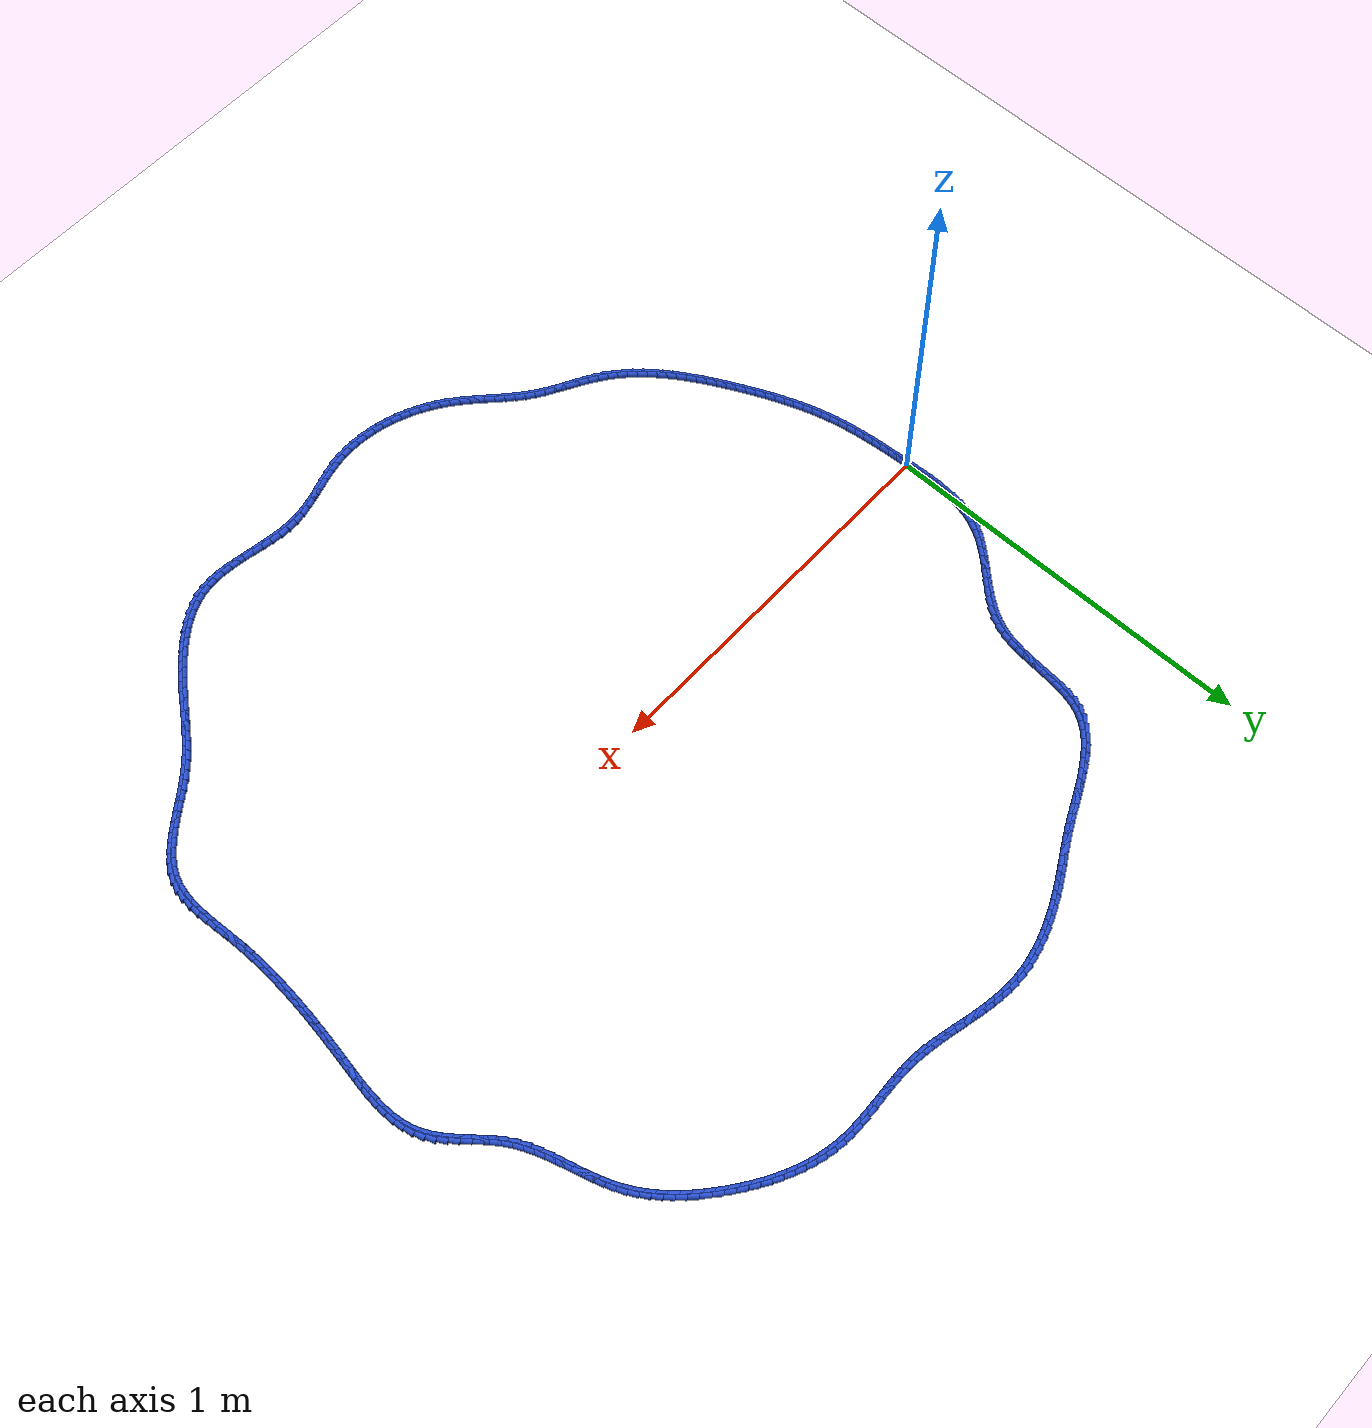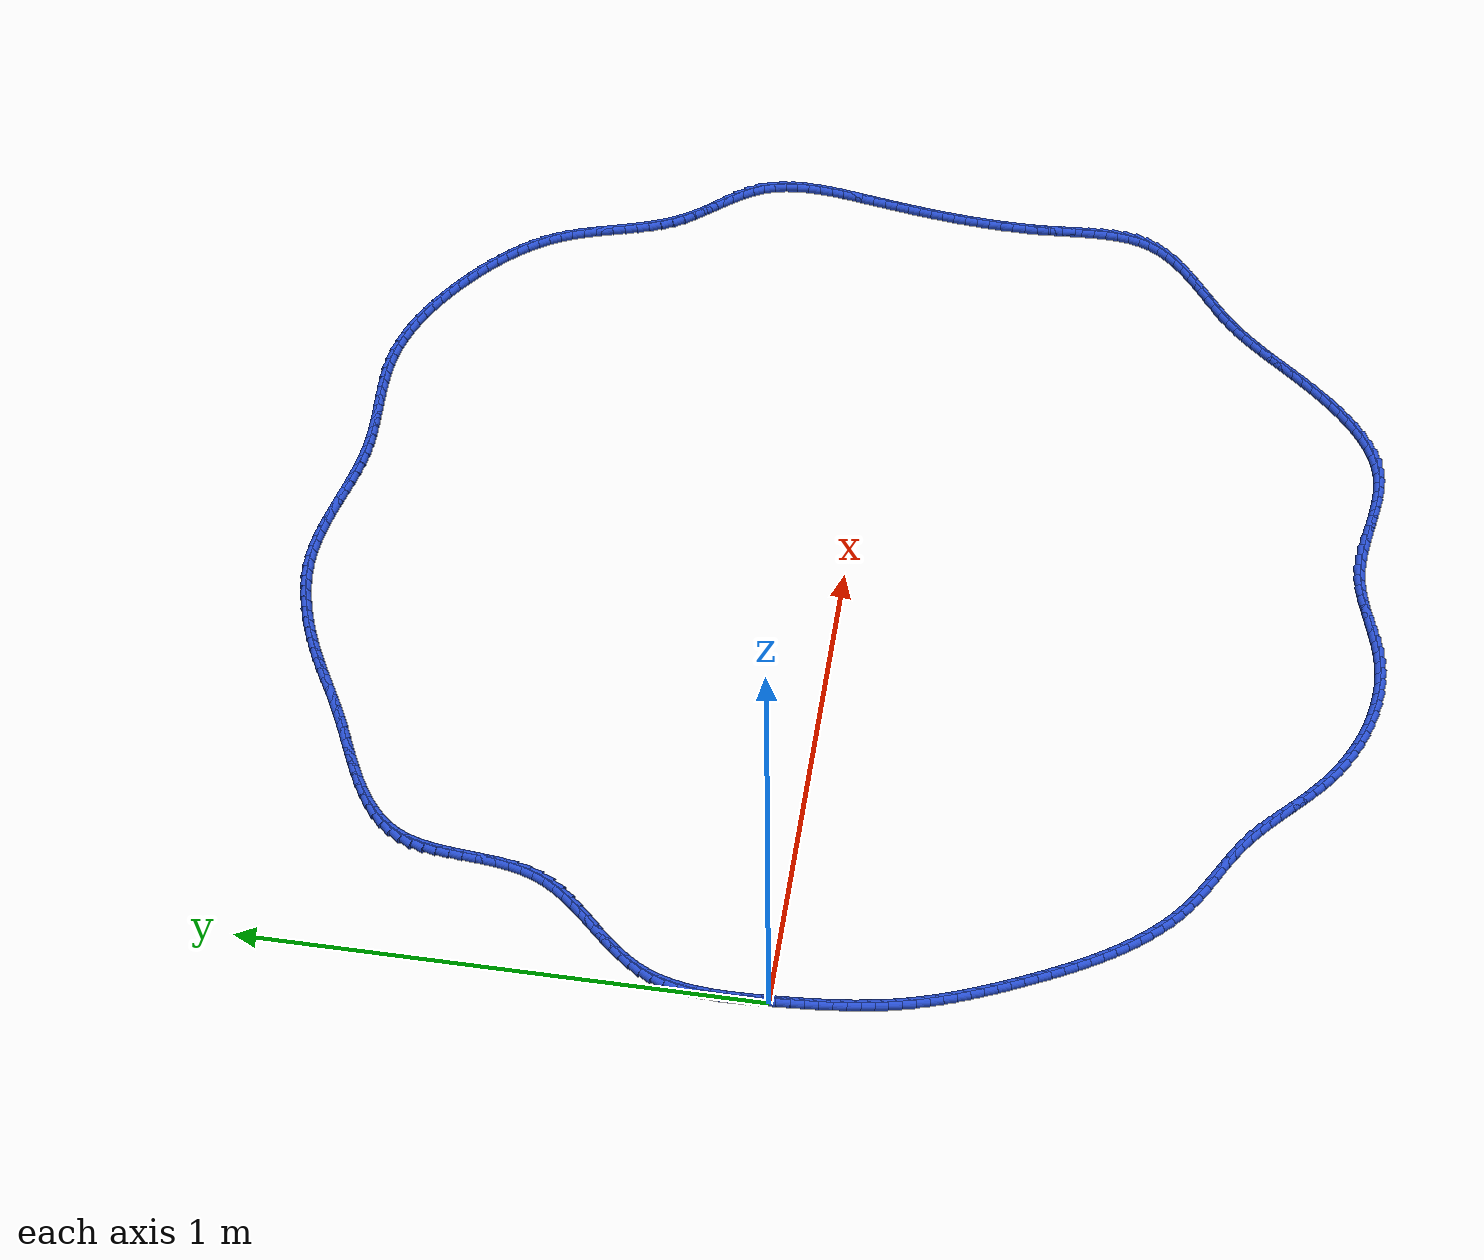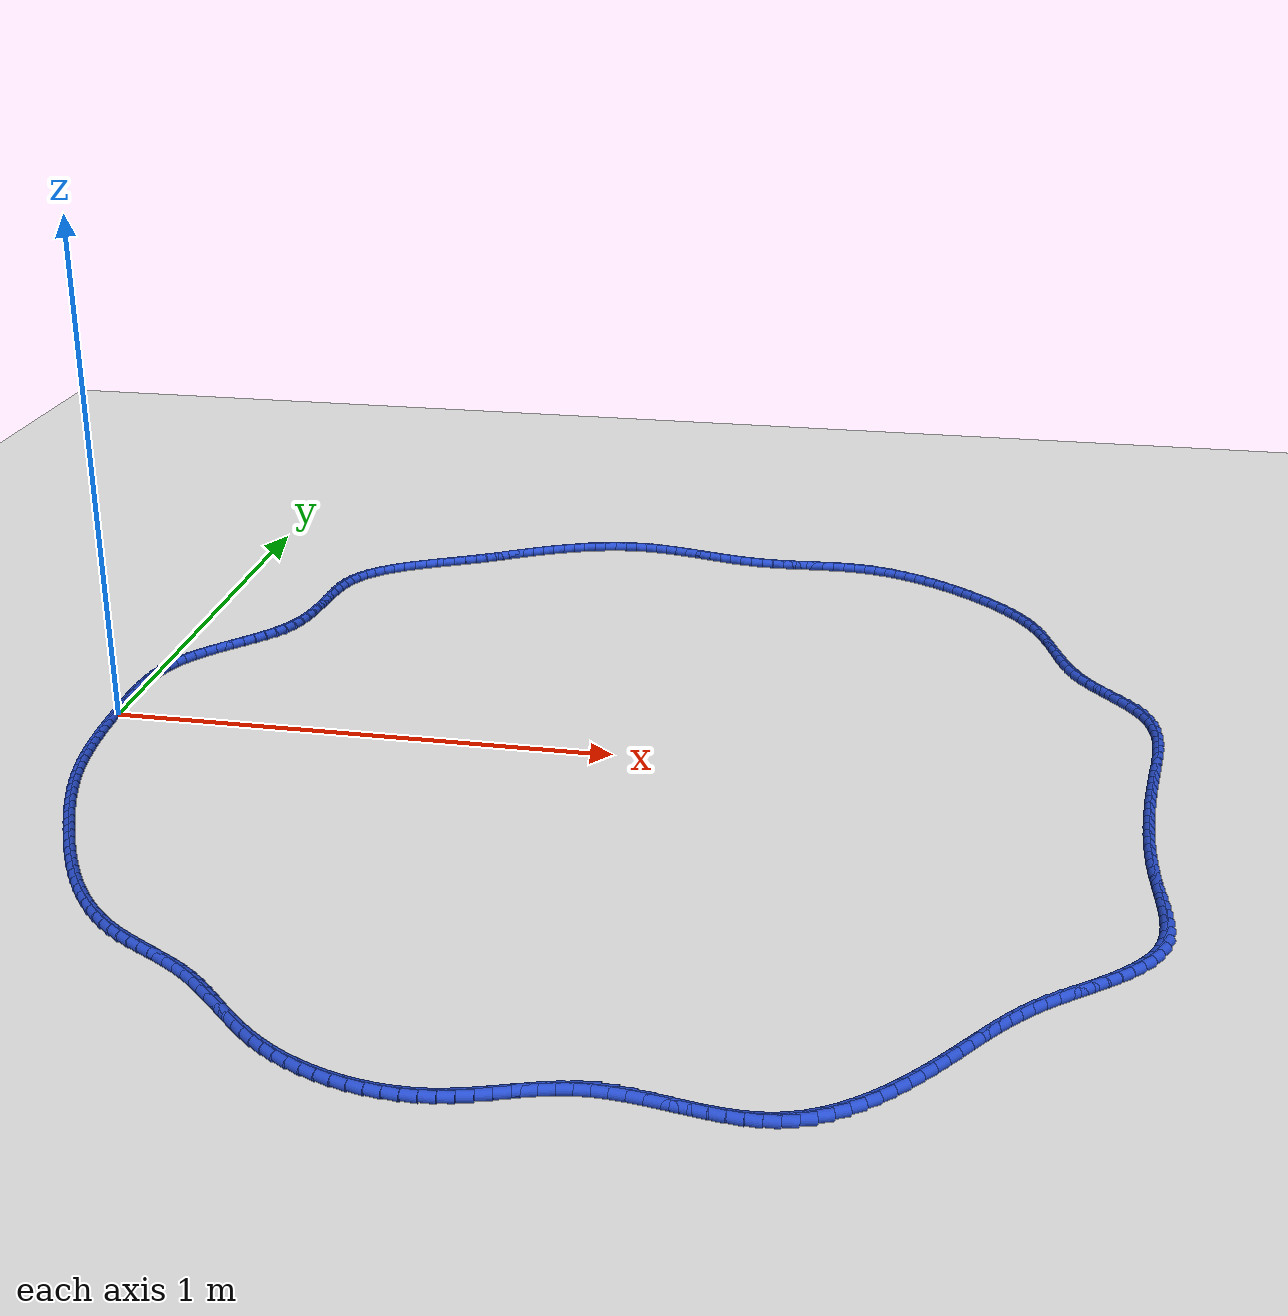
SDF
<sdf version="1.6">
 <world name="default">
  <light name="sun" type="directional">
   <pose>0 0 10 0 -0 0</pose>
   <diffuse>0.8 0.8 0.8 1</diffuse>
   <specular>0.2 0.2 0.2 1</specular>
   <attenuation>
    <range>1000</range>
    <constant>0.9</constant>
    <linear>0.01</linear>
    <quadratic>0.001</quadratic>
   </attenuation>
   <direction>-0.5 0.1 -0.9</direction>
  </light>
  <model name="ground_plane">
   <static>1</static>
   <link name="link">
    <collision name="collision">
     <geometry><plane><normal>0 0 1</normal><size>100 100</size></plane></geometry>
     <surface><friction><ode><mu>100</mu><mu2>50</mu2></ode></friction></surface>
    </collision>
    <visual name="visual">
     <cast_shadows>0</cast_shadows>
     <geometry><plane><normal>0 0 1</normal><size>100 100</size></plane></geometry>
     <material>
      <script><uri>file://media/materials/scripts/gazebo.material</uri><name>Gazebo/WhiteGlow</name></script>
     </material>
    </visual>
   </link>
  </model>
  <gravity>0 0 -9.8</gravity>
  <magnetic_field>6e-06 2.3e-05 -4.2e-05</magnetic_field>
  <atmosphere type="adiabatic"/>
  <physics name="default_physics" default="0" type="ode">
   <max_step_size>0.001</max_step_size>
   <real_time_factor>1</real_time_factor>
   <real_time_update_rate>1000</real_time_update_rate>
  </physics>
  <scene><ambient>0.4 0.4 0.4 1</ambient><background>0.7 0.7 0.7 1</background><shadows>1</shadows></scene>
  <spherical_coordinates>
   <surface_model>EARTH_WGS84</surface_model>
   <latitude_deg>0</latitude_deg>
   <longitude_deg>0</longitude_deg>
   <elevation>0</elevation>
   <heading_deg>0</heading_deg>
  </spherical_coordinates>
  <model name="line">
   <link name="link_0">
    <pose>2.168404344971009e-19 -1.3877787807814457e-17 0.01 0 1.57 -1.525572002247885</pose>
    <collision name="collision">
     <geometry><cylinder><radius>0.01</radius><length>0.08</length></cylinder></geometry>
    </collision>
    <visual name="visual">
     <material>
      <script><name>Gazebo/Blue</name><uri>file://media/materials/scripts/gazebo.material</uri></script>
     </material>
     <geometry><cylinder><radius>0.01</radius><length>0.08</length></cylinder></geometry>
    </visual>
   </link>
   <link name="link_1">
    <pose>-0.001192701186760146 0.026355019515203342 0.01 0 1.57 -1.5404109730915096</pose>
    <collision name="collision">
     <geometry><cylinder><radius>0.01</radius><length>0.08</length></cylinder></geometry>
    </collision>
    <visual name="visual">
     <material>
      <script><name>Gazebo/Blue</name><uri>file://media/materials/scripts/gazebo.material</uri></script>
     </material>
     <geometry><cylinder><radius>0.01</radius><length>0.08</length></cylinder></geometry>
    </visual>
   </link>
   <link name="link_2">
    <pose>-0.001996711604233633 0.0528073350155297 0.01 0 1.57 -1.5643912887022506</pose>
    <collision name="collision">
     <geometry><cylinder><radius>0.01</radius><length>0.08</length></cylinder></geometry>
    </collision>
    <visual name="visual">
     <material>
      <script><name>Gazebo/Blue</name><uri>file://media/materials/scripts/gazebo.material</uri></script>
     </material>
     <geometry><cylinder><radius>0.01</radius><length>0.08</length></cylinder></geometry>
    </visual>
   </link>
   <link name="link_3">
    <pose>-0.00216583373129672 0.07921152057897023 0.01 0 1.57 1.5436398385513426</pose>
    <collision name="collision">
     <geometry><cylinder><radius>0.01</radius><length>0.08</length></cylinder></geometry>
    </collision>
    <visual name="visual">
     <material>
      <script><name>Gazebo/Blue</name><uri>file://media/materials/scripts/gazebo.material</uri></script>
     </material>
     <geometry><cylinder><radius>0.01</radius><length>0.08</length></cylinder></geometry>
    </visual>
   </link>
   <link name="link_4">
    <pose>-0.001453870046825666 0.10542215028351616 0.01 0 1.57 1.499824508919937</pose>
    <collision name="collision">
     <geometry><cylinder><radius>0.01</radius><length>0.08</length></cylinder></geometry>
    </collision>
    <visual name="visual">
     <material>
      <script><name>Gazebo/Blue</name><uri>file://media/materials/scripts/gazebo.material</uri></script>
     </material>
     <geometry><cylinder><radius>0.01</radius><length>0.08</length></cylinder></geometry>
    </visual>
   </link>
   <link name="link_5">
    <pose>0.0003853769703032672 0.1312937982071587 0.01 0 1.57 1.4449165321309105</pose>
    <collision name="collision">
     <geometry><cylinder><radius>0.01</radius><length>0.08</length></cylinder></geometry>
    </collision>
    <visual name="visual">
     <material>
      <script><name>Gazebo/Blue</name><uri>file://media/materials/scripts/gazebo.material</uri></script>
     </material>
     <geometry><cylinder><radius>0.01</radius><length>0.08</length></cylinder></geometry>
    </visual>
   </link>
   <link name="link_6">
    <pose>0.0035981048412138212 0.15668103842788905 0.01 0 1.57 1.3780297026481514</pose>
    <collision name="collision">
     <geometry><cylinder><radius>0.01</radius><length>0.08</length></cylinder></geometry>
    </collision>
    <visual name="visual">
     <material>
      <script><name>Gazebo/Blue</name><uri>file://media/materials/scripts/gazebo.material</uri></script>
     </material>
     <geometry><cylinder><radius>0.01</radius><length>0.08</length></cylinder></geometry>
    </visual>
   </link>
   <link name="link_7">
    <pose>0.00843051108702974 0.18143844502369835 0.01 0 1.57 1.2984342029268958</pose>
    <collision name="collision">
     <geometry><cylinder><radius>0.01</radius><length>0.08</length></cylinder></geometry>
    </collision>
    <visual name="visual">
     <material>
      <script><name>Gazebo/Blue</name><uri>file://media/materials/scripts/gazebo.material</uri></script>
     </material>
     <geometry><cylinder><radius>0.01</radius><length>0.08</length></cylinder></geometry>
    </visual>
   </link>
   <link name="link_8">
    <pose>0.015128793228874757 0.20542059207257785 0.01 0 1.57 1.205869643138353</pose>
    <collision name="collision">
     <geometry><cylinder><radius>0.01</radius><length>0.08</length></cylinder></geometry>
    </collision>
    <visual name="visual">
     <material>
      <script><name>Gazebo/Blue</name><uri>file://media/materials/scripts/gazebo.material</uri></script>
     </material>
     <geometry><cylinder><radius>0.01</radius><length>0.08</length></cylinder></geometry>
    </visual>
   </link>
   <link name="link_9">
    <pose>0.023939148787872615 0.22848205365251878 0.01 0 1.57 1.101675434037345</pose>
    <collision name="collision">
     <geometry><cylinder><radius>0.01</radius><length>0.08</length></cylinder></geometry>
    </collision>
    <visual name="visual">
     <material>
      <script><name>Gazebo/Blue</name><uri>file://media/materials/scripts/gazebo.material</uri></script>
     </material>
     <geometry><cylinder><radius>0.01</radius><length>0.08</length></cylinder></geometry>
    </visual>
   </link>
   <link name="link_10">
    <pose>0.03509188397794311 0.2504856154587042 0.01 0 1.57 1.00310683562596</pose>
    <collision name="collision">
     <geometry><cylinder><radius>0.01</radius><length>0.08</length></cylinder></geometry>
    </collision>
    <visual name="visual">
     <material>
      <script><name>Gazebo/Blue</name><uri>file://media/materials/scripts/gazebo.material</uri></script>
     </material>
     <geometry><cylinder><radius>0.01</radius><length>0.08</length></cylinder></geometry>
    </visual>
   </link>
   <link name="link_11">
    <pose>0.04847463441397935 0.2714711335648583 0.01 0 1.57 0.926142022619364</pose>
    <collision name="collision">
     <geometry><cylinder><radius>0.01</radius><length>0.08</length></cylinder></geometry>
    </collision>
    <visual name="visual">
     <material>
      <script><name>Gazebo/Blue</name><uri>file://media/materials/scripts/gazebo.material</uri></script>
     </material>
     <geometry><cylinder><radius>0.01</radius><length>0.08</length></cylinder></geometry>
    </visual>
   </link>
   <link name="link_12">
    <pose>0.06364458784133728 0.29164921849376924 0.01 0 1.57 0.870737300951593</pose>
    <collision name="collision">
     <geometry><cylinder><radius>0.01</radius><length>0.08</length></cylinder></geometry>
    </collision>
    <visual name="visual">
     <material>
      <script><name>Gazebo/Blue</name><uri>file://media/materials/scripts/gazebo.material</uri></script>
     </material>
     <geometry><cylinder><radius>0.01</radius><length>0.08</length></cylinder></geometry>
    </visual>
   </link>
   <link name="link_13">
    <pose>0.08014548625503527 0.3112374286771168 0.01 0 1.57 0.8356491842077733</pose>
    <collision name="collision">
     <geometry><cylinder><radius>0.01</radius><length>0.08</length></cylinder></geometry>
    </collision>
    <visual name="visual">
     <material>
      <script><name>Gazebo/Blue</name><uri>file://media/materials/scripts/gazebo.material</uri></script>
     </material>
     <geometry><cylinder><radius>0.01</radius><length>0.08</length></cylinder></geometry>
    </visual>
   </link>
   <link name="link_14">
    <pose>0.09752107165009188 0.33045332254658116 0.01 0 1.57 0.8197657534150228</pose>
    <collision name="collision">
     <geometry><cylinder><radius>0.01</radius><length>0.08</length></cylinder></geometry>
    </collision>
    <visual name="visual">
     <material>
      <script><name>Gazebo/Blue</name><uri>file://media/materials/scripts/gazebo.material</uri></script>
     </material>
     <geometry><cylinder><radius>0.01</radius><length>0.08</length></cylinder></geometry>
    </visual>
   </link>
   <link name="link_15">
    <pose>0.11531508602152549 0.3495144585338423 0.01 0 1.57 0.8224675810721056</pose>
    <collision name="collision">
     <geometry><cylinder><radius>0.01</radius><length>0.08</length></cylinder></geometry>
    </collision>
    <visual name="visual">
     <material>
      <script><name>Gazebo/Blue</name><uri>file://media/materials/scripts/gazebo.material</uri></script>
     </material>
     <geometry><cylinder><radius>0.01</radius><length>0.08</length></cylinder></geometry>
    </visual>
   </link>
   <link name="link_16">
    <pose>0.13307127136435454 0.36863839507058005 0.01 0 1.57 0.8437558200754279</pose>
    <collision name="collision">
     <geometry><cylinder><radius>0.01</radius><length>0.08</length></cylinder></geometry>
    </collision>
    <visual name="visual">
     <material>
      <script><name>Gazebo/Blue</name><uri>file://media/materials/scripts/gazebo.material</uri></script>
     </material>
     <geometry><cylinder><radius>0.01</radius><length>0.08</length></cylinder></geometry>
    </visual>
   </link>
   <link name="link_17">
    <pose>0.15033336967359756 0.38804269058847474 0.01 0 1.57 0.8842209202165721</pose>
    <collision name="collision">
     <geometry><cylinder><radius>0.01</radius><length>0.08</length></cylinder></geometry>
    </collision>
    <visual name="visual">
     <material>
      <script><name>Gazebo/Blue</name><uri>file://media/materials/scripts/gazebo.material</uri></script>
     </material>
     <geometry><cylinder><radius>0.01</radius><length>0.08</length></cylinder></geometry>
    </visual>
   </link>
   <link name="link_18">
    <pose>0.1666451229442729 0.40794490351920604 0.01 0 1.57 0.9448461479382917</pose>
    <collision name="collision">
     <geometry><cylinder><radius>0.01</radius><length>0.08</length></cylinder></geometry>
    </collision>
    <visual name="visual">
     <material>
      <script><name>Gazebo/Blue</name><uri>file://media/materials/scripts/gazebo.material</uri></script>
     </material>
     <geometry><cylinder><radius>0.01</radius><length>0.08</length></cylinder></geometry>
    </visual>
   </link>
   <link name="link_19">
    <pose>0.181550273171399 0.42856259229445404 0.01 0 1.57 1.0265691454415318</pose>
    <collision name="collision">
     <geometry><cylinder><radius>0.01</radius><length>0.08</length></cylinder></geometry>
    </collision>
    <visual name="visual">
     <material>
      <script><name>Gazebo/Blue</name><uri>file://media/materials/scripts/gazebo.material</uri></script>
     </material>
     <geometry><cylinder><radius>0.01</radius><length>0.08</length></cylinder></geometry>
    </visual>
   </link>
   <link name="link_20">
    <pose>0.19459256234999442 0.45011331534589893 0.01 0 1.57 1.1295042287333261</pose>
    <collision name="collision">
     <geometry><cylinder><radius>0.01</radius><length>0.08</length></cylinder></geometry>
    </collision>
    <visual name="visual">
     <material>
      <script><name>Gazebo/Blue</name><uri>file://media/materials/scripts/gazebo.material</uri></script>
     </material>
     <geometry><cylinder><radius>0.01</radius><length>0.08</length></cylinder></geometry>
    </visual>
   </link>
   <link name="link_21">
    <pose>0.20531575054510487 0.4728146217601626 0.01 0 1.57 1.2436033963603357</pose>
    <collision name="collision">
     <geometry><cylinder><radius>0.01</radius><length>0.08</length></cylinder></geometry>
    </collision>
    <visual name="visual">
     <material>
      <script><name>Gazebo/Blue</name><uri>file://media/materials/scripts/gazebo.material</uri></script>
     </material>
     <geometry><cylinder><radius>0.01</radius><length>0.08</length></cylinder></geometry>
    </visual>
   </link>
   <link name="link_22">
    <pose>0.213451697641281 0.4967867833108267 0.01 0 1.57 1.3380486251099197</pose>
    <collision name="collision">
     <geometry><cylinder><radius>0.01</radius><length>0.08</length></cylinder></geometry>
    </collision>
    <visual name="visual">
     <material>
      <script><name>Gazebo/Blue</name><uri>file://media/materials/scripts/gazebo.material</uri></script>
     </material>
     <geometry><cylinder><radius>0.01</radius><length>0.08</length></cylinder></geometry>
    </visual>
   </link>
   <link name="link_23">
    <pose>0.21938400579576403 0.5218130180876943 0.01 0 1.57 1.4073494618705584</pose>
    <collision name="collision">
     <geometry><cylinder><radius>0.01</radius><length>0.08</length></cylinder></geometry>
    </collision>
    <visual name="visual">
     <material>
      <script><name>Gazebo/Blue</name><uri>file://media/materials/scripts/gazebo.material</uri></script>
     </material>
     <geometry><cylinder><radius>0.01</radius><length>0.08</length></cylinder></geometry>
    </visual>
   </link>
   <link name="link_24">
    <pose>0.2236373378716247 0.5476035935181236 0.01 0 1.57 1.453349717159858</pose>
    <collision name="collision">
     <geometry><cylinder><radius>0.01</radius><length>0.08</length></cylinder></geometry>
    </collision>
    <visual name="visual">
     <material>
      <script><name>Gazebo/Blue</name><uri>file://media/materials/scripts/gazebo.material</uri></script>
     </material>
     <geometry><cylinder><radius>0.01</radius><length>0.08</length></cylinder></geometry>
    </visual>
   </link>
   <link name="link_25">
    <pose>0.2267363567319338 0.573868777029472 0.01 0 1.57 1.4777064991671223</pose>
    <collision name="collision">
     <geometry><cylinder><radius>0.01</radius><length>0.08</length></cylinder></geometry>
    </collision>
    <visual name="visual">
     <material>
      <script><name>Gazebo/Blue</name><uri>file://media/materials/scripts/gazebo.material</uri></script>
     </material>
     <geometry><cylinder><radius>0.01</radius><length>0.08</length></cylinder></geometry>
    </visual>
   </link>
   <link name="link_26">
    <pose>0.2292057252397621 0.600318836049098 0.01 0 1.57 1.4812899471059946</pose>
    <collision name="collision">
     <geometry><cylinder><radius>0.01</radius><length>0.08</length></cylinder></geometry>
    </collision>
    <visual name="visual">
     <material>
      <script><name>Gazebo/Blue</name><uri>file://media/materials/scripts/gazebo.material</uri></script>
     </material>
     <geometry><cylinder><radius>0.01</radius><length>0.08</length></cylinder></geometry>
    </visual>
   </link>
   <link name="link_27">
    <pose>0.23157010625818045 0.6266640380043592 0.01 0 1.57 1.463922223845543</pose>
    <collision name="collision">
     <geometry><cylinder><radius>0.01</radius><length>0.08</length></cylinder></geometry>
    </collision>
    <visual name="visual">
     <material>
      <script><name>Gazebo/Blue</name><uri>file://media/materials/scripts/gazebo.material</uri></script>
     </material>
     <geometry><cylinder><radius>0.01</radius><length>0.08</length></cylinder></geometry>
    </visual>
   </link>
   <link name="link_28">
    <pose>0.23435416265025946 0.6526146503226133 0.01 0 1.57 1.4242896303692543</pose>
    <collision name="collision">
     <geometry><cylinder><radius>0.01</radius><length>0.08</length></cylinder></geometry>
    </collision>
    <visual name="visual">
     <material>
      <script><name>Gazebo/Blue</name><uri>file://media/materials/scripts/gazebo.material</uri></script>
     </material>
     <geometry><cylinder><radius>0.01</radius><length>0.08</length></cylinder></geometry>
    </visual>
   </link>
   <link name="link_29">
    <pose>0.23808255727907013 0.6778809404312189 0.01 0 1.57 1.3600211578399588</pose>
    <collision name="collision">
     <geometry><cylinder><radius>0.01</radius><length>0.08</length></cylinder></geometry>
    </collision>
    <visual name="visual">
     <material>
      <script><name>Gazebo/Blue</name><uri>file://media/materials/scripts/gazebo.material</uri></script>
     </material>
     <geometry><cylinder><radius>0.01</radius><length>0.08</length></cylinder></geometry>
    </visual>
   </link>
   <link name="link_30">
    <pose>0.24327995300768301 0.7021731757575332 0.01 0 1.57 1.2681223451279466</pose>
    <collision name="collision">
     <geometry><cylinder><radius>0.01</radius><length>0.08</length></cylinder></geometry>
    </collision>
    <visual name="visual">
     <material>
      <script><name>Gazebo/Blue</name><uri>file://media/materials/scripts/gazebo.material</uri></script>
     </material>
     <geometry><cylinder><radius>0.01</radius><length>0.08</length></cylinder></geometry>
    </visual>
   </link>
   <link name="link_31">
    <pose>0.2504710126991691 0.7252016237289144 0.01 0 1.57 1.1461808343119926</pose>
    <collision name="collision">
     <geometry><cylinder><radius>0.01</radius><length>0.08</length></cylinder></geometry>
    </collision>
    <visual name="visual">
     <material>
      <script><name>Gazebo/Blue</name><uri>file://media/materials/scripts/gazebo.material</uri></script>
     </material>
     <geometry><cylinder><radius>0.01</radius><length>0.08</length></cylinder></geometry>
    </visual>
   </link>
   <link name="link_32">
    <pose>0.2601802850565578 0.7466766150641043 0.01 0 1.57 1.0037048574788439</pose>
    <collision name="collision">
     <geometry><cylinder><radius>0.01</radius><length>0.08</length></cylinder></geometry>
    </collision>
    <visual name="visual">
     <material>
      <script><name>Gazebo/Blue</name><uri>file://media/materials/scripts/gazebo.material</uri></script>
     </material>
     <geometry><cylinder><radius>0.01</radius><length>0.08</length></cylinder></geometry>
    </visual>
   </link>
   <link name="link_33">
    <pose>0.27274826976356265 0.7664105189619083 0.01 0 1.57 0.872362219551045</pose>
    <collision name="collision">
     <geometry><cylinder><radius>0.01</radius><length>0.08</length></cylinder></geometry>
    </collision>
    <visual name="visual">
     <material>
      <script><name>Gazebo/Blue</name><uri>file://media/materials/scripts/gazebo.material</uri></script>
     </material>
     <geometry><cylinder><radius>0.01</radius><length>0.08</length></cylinder></geometry>
    </visual>
   </link>
   <link name="link_34">
    <pose>0.28795750023784905 0.7845250462841665 0.01 0 1.57 0.760481119555493</pose>
    <collision name="collision">
     <geometry><cylinder><radius>0.01</radius><length>0.08</length></cylinder></geometry>
    </collision>
    <visual name="visual">
     <material>
      <script><name>Gazebo/Blue</name><uri>file://media/materials/scripts/gazebo.material</uri></script>
     </material>
     <geometry><cylinder><radius>0.01</radius><length>0.08</length></cylinder></geometry>
    </visual>
   </link>
   <link name="link_35">
    <pose>0.30548517366280903 0.8012003072761038 0.01 0 1.57 0.6683828949023575</pose>
    <collision name="collision">
     <geometry><cylinder><radius>0.01</radius><length>0.08</length></cylinder></geometry>
    </collision>
    <visual name="visual">
     <material>
      <script><name>Gazebo/Blue</name><uri>file://media/materials/scripts/gazebo.material</uri></script>
     </material>
     <geometry><cylinder><radius>0.01</radius><length>0.08</length></cylinder></geometry>
    </visual>
   </link>
   <link name="link_36">
    <pose>0.3250084872218347 0.8166164121829464 0.01 0 1.57 0.5947102658332788</pose>
    <collision name="collision">
     <geometry><cylinder><radius>0.01</radius><length>0.08</length></cylinder></geometry>
    </collision>
    <visual name="visual">
     <material>
      <script><name>Gazebo/Blue</name><uri>file://media/materials/scripts/gazebo.material</uri></script>
     </material>
     <geometry><cylinder><radius>0.01</radius><length>0.08</length></cylinder></geometry>
    </visual>
   </link>
   <link name="link_37">
    <pose>0.3462046380983184 0.8309534712499199 0.01 0 1.57 0.537492670768596</pose>
    <collision name="collision">
     <geometry><cylinder><radius>0.01</radius><length>0.08</length></cylinder></geometry>
    </collision>
    <visual name="visual">
     <material>
      <script><name>Gazebo/Blue</name><uri>file://media/materials/scripts/gazebo.material</uri></script>
     </material>
     <geometry><cylinder><radius>0.01</radius><length>0.08</length></cylinder></geometry>
    </visual>
   </link>
   <link name="link_38">
    <pose>0.3687508234756525 0.8443915947222497 0.01 0 1.57 0.4947933664515222</pose>
    <collision name="collision">
     <geometry><cylinder><radius>0.01</radius><length>0.08</length></cylinder></geometry>
    </collision>
    <visual name="visual">
     <material>
      <script><name>Gazebo/Blue</name><uri>file://media/materials/scripts/gazebo.material</uri></script>
     </material>
     <geometry><cylinder><radius>0.01</radius><length>0.08</length></cylinder></geometry>
    </visual>
   </link>
   <link name="link_39">
    <pose>0.39232424053722903 0.8571108928451616 0.01 0 1.57 0.46501944249125043</pose>
    <collision name="collision">
     <geometry><cylinder><radius>0.01</radius><length>0.08</length></cylinder></geometry>
    </collision>
    <visual name="visual">
     <material>
      <script><name>Gazebo/Blue</name><uri>file://media/materials/scripts/gazebo.material</uri></script>
     </material>
     <geometry><cylinder><radius>0.01</radius><length>0.08</length></cylinder></geometry>
    </visual>
   </link>
   <link name="link_40">
    <pose>0.41660208646644015 0.8692914758638816 0.01 0 1.57 0.4470397094712492</pose>
    <collision name="collision">
     <geometry><cylinder><radius>0.01</radius><length>0.08</length></cylinder></geometry>
    </collision>
    <visual name="visual">
     <material>
      <script><name>Gazebo/Blue</name><uri>file://media/materials/scripts/gazebo.material</uri></script>
     </material>
     <geometry><cylinder><radius>0.01</radius><length>0.08</length></cylinder></geometry>
    </visual>
   </link>
   <link name="link_41">
    <pose>0.4412615584466781 0.8811134540236347 0.01 0 1.57 0.4402182625999187</pose>
    <collision name="collision">
     <geometry><cylinder><radius>0.01</radius><length>0.08</length></cylinder></geometry>
    </collision>
    <visual name="visual">
     <material>
      <script><name>Gazebo/Blue</name><uri>file://media/materials/scripts/gazebo.material</uri></script>
     </material>
     <geometry><cylinder><radius>0.01</radius><length>0.08</length></cylinder></geometry>
    </visual>
   </link>
   <link name="link_42">
    <pose>0.4659798536613352 0.8927569375696472 0.01 0 1.57 0.44442544236932796</pose>
    <collision name="collision">
     <geometry><cylinder><radius>0.01</radius><length>0.08</length></cylinder></geometry>
    </collision>
    <visual name="visual">
     <material>
      <script><name>Gazebo/Blue</name><uri>file://media/materials/scripts/gazebo.material</uri></script>
     </material>
     <geometry><cylinder><radius>0.01</radius><length>0.08</length></cylinder></geometry>
    </visual>
   </link>
   <link name="link_43">
    <pose>0.49043416929380373 0.9044020367471445 0.01 0 1.57 0.4600517057744478</pose>
    <collision name="collision">
     <geometry><cylinder><radius>0.01</radius><length>0.08</length></cylinder></geometry>
    </collision>
    <visual name="visual">
     <material>
      <script><name>Gazebo/Blue</name><uri>file://media/materials/scripts/gazebo.material</uri></script>
     </material>
     <geometry><cylinder><radius>0.01</radius><length>0.08</length></cylinder></geometry>
    </visual>
   </link>
   <link name="link_44">
    <pose>0.514301840376939 0.9162287820758385 0.01 0 1.57 0.48325954570123025</pose>
    <collision name="collision">
     <geometry><cylinder><radius>0.01</radius><length>0.08</length></cylinder></geometry>
    </collision>
    <visual name="visual">
     <material>
      <script><name>Gazebo/Blue</name><uri>file://media/materials/scripts/gazebo.material</uri></script>
     </material>
     <geometry><cylinder><radius>0.01</radius><length>0.08</length></cylinder></geometry>
    </visual>
   </link>
   <link name="link_45">
    <pose>0.5373878149170888 0.928343398856114 0.01 0 1.57 0.5007259656540738</pose>
    <collision name="collision">
     <geometry><cylinder><radius>0.01</radius><length>0.08</length></cylinder></geometry>
    </collision>
    <visual name="visual">
     <material>
      <script><name>Gazebo/Blue</name><uri>file://media/materials/scripts/gazebo.material</uri></script>
     </material>
     <geometry><cylinder><radius>0.01</radius><length>0.08</length></cylinder></geometry>
    </visual>
   </link>
   <link name="link_46">
    <pose>0.5598608825974675 0.940641683824343 0.01 0 1.57 0.5093921789110664</pose>
    <collision name="collision">
     <geometry><cylinder><radius>0.01</radius><length>0.08</length></cylinder></geometry>
    </collision>
    <visual name="visual">
     <material>
      <script><name>Gazebo/Blue</name><uri>file://media/materials/scripts/gazebo.material</uri></script>
     </material>
     <geometry><cylinder><radius>0.01</radius><length>0.08</length></cylinder></geometry>
    </visual>
   </link>
   <link name="link_47">
    <pose>0.5819542509646431 0.9529821775163453 0.01 0 1.57 0.5087867753595292</pose>
    <collision name="collision">
     <geometry><cylinder><radius>0.01</radius><length>0.08</length></cylinder></geometry>
    </collision>
    <visual name="visual">
     <material>
      <script><name>Gazebo/Blue</name><uri>file://media/materials/scripts/gazebo.material</uri></script>
     </material>
     <geometry><cylinder><radius>0.01</radius><length>0.08</length></cylinder></geometry>
    </visual>
   </link>
   <link name="link_48">
    <pose>0.6039011275651838 0.9652234204679407 0.01 0 1.57 0.49872423113759856</pose>
    <collision name="collision">
     <geometry><cylinder><radius>0.01</radius><length>0.08</length></cylinder></geometry>
    </collision>
    <visual name="visual">
     <material>
      <script><name>Gazebo/Blue</name><uri>file://media/materials/scripts/gazebo.material</uri></script>
     </material>
     <geometry><cylinder><radius>0.01</radius><length>0.08</length></cylinder></geometry>
    </visual>
   </link>
   <link name="link_49">
    <pose>0.6259347199456576 0.9772239532149499 0.01 0 1.57 0.47932682582244573</pose>
    <collision name="collision">
     <geometry><cylinder><radius>0.01</radius><length>0.08</length></cylinder></geometry>
    </collision>
    <visual name="visual">
     <material>
      <script><name>Gazebo/Blue</name><uri>file://media/materials/scripts/gazebo.material</uri></script>
     </material>
     <geometry><cylinder><radius>0.01</radius><length>0.08</length></cylinder></geometry>
    </visual>
   </link>
   <link name="link_50">
    <pose>0.6482882356526329 0.9888423162931926 0.01 0 1.57 0.4513516744903677</pose>
    <collision name="collision">
     <geometry><cylinder><radius>0.01</radius><length>0.08</length></cylinder></geometry>
    </collision>
    <visual name="visual">
     <material>
      <script><name>Gazebo/Blue</name><uri>file://media/materials/scripts/gazebo.material</uri></script>
     </material>
     <geometry><cylinder><radius>0.01</radius><length>0.08</length></cylinder></geometry>
    </visual>
   </link>
   <link name="link_51">
    <pose>0.6711771882753453 0.999937123408897 0.01 0 1.57 0.4184259051370871</pose>
    <collision name="collision">
     <geometry><cylinder><radius>0.01</radius><length>0.08</length></cylinder></geometry>
    </collision>
    <visual name="visual">
     <material>
      <script><name>Gazebo/Blue</name><uri>file://media/materials/scripts/gazebo.material</uri></script>
     </material>
     <geometry><cylinder><radius>0.01</radius><length>0.08</length></cylinder></geometry>
    </visual>
   </link>
   <link name="link_52">
    <pose>0.6946333528191165 1.0103677480885422 0.01 0 1.57 0.3822245574260171</pose>
    <collision name="collision">
     <geometry><cylinder><radius>0.01</radius><length>0.08</length></cylinder></geometry>
    </collision>
    <visual name="visual">
     <material>
      <script><name>Gazebo/Blue</name><uri>file://media/materials/scripts/gazebo.material</uri></script>
     </material>
     <geometry><cylinder><radius>0.01</radius><length>0.08</length></cylinder></geometry>
    </visual>
   </link>
   <link name="link_53">
    <pose>0.7185796181627329 1.0199940141390145 0.01 0 1.57 0.34238707417006126</pose>
    <collision name="collision">
     <geometry><cylinder><radius>0.01</radius><length>0.08</length></cylinder></geometry>
    </collision>
    <visual name="visual">
     <material>
      <script><name>Gazebo/Blue</name><uri>file://media/materials/scripts/gazebo.material</uri></script>
     </material>
     <geometry><cylinder><radius>0.01</radius><length>0.08</length></cylinder></geometry>
    </visual>
   </link>
   <link name="link_54">
    <pose>0.7429374467315265 1.0286757512660603 0.01 0 1.57 0.29849345570736374</pose>
    <collision name="collision">
     <geometry><cylinder><radius>0.01</radius><length>0.08</length></cylinder></geometry>
    </collision>
    <visual name="visual">
     <material>
      <script><name>Gazebo/Blue</name><uri>file://media/materials/scripts/gazebo.material</uri></script>
     </material>
     <geometry><cylinder><radius>0.01</radius><length>0.08</length></cylinder></geometry>
    </visual>
   </link>
   <link name="link_55">
    <pose>0.7676283009508278 1.0362727891754246 0.01 0 1.57 0.25009697159213545</pose>
    <collision name="collision">
     <geometry><cylinder><radius>0.01</radius><length>0.08</length></cylinder></geometry>
    </collision>
    <visual name="visual">
     <material>
      <script><name>Gazebo/Blue</name><uri>file://media/materials/scripts/gazebo.material</uri></script>
     </material>
     <geometry><cylinder><radius>0.01</radius><length>0.08</length></cylinder></geometry>
    </visual>
   </link>
   <link name="link_56">
    <pose>0.7925736432459684 1.042644957572854 0.01 0 1.57 0.19673981012162825</pose>
    <collision name="collision">
     <geometry><cylinder><radius>0.01</radius><length>0.08</length></cylinder></geometry>
    </collision>
    <visual name="visual">
     <material>
      <script><name>Gazebo/Blue</name><uri>file://media/materials/scripts/gazebo.material</uri></script>
     </material>
     <geometry><cylinder><radius>0.01</radius><length>0.08</length></cylinder></geometry>
    </visual>
   </link>
   <link name="link_57">
    <pose>0.8176949360422789 1.0476520861640937 0.01 0 1.57 0.13797958817576</pose>
    <collision name="collision">
     <geometry><cylinder><radius>0.01</radius><length>0.08</length></cylinder></geometry>
    </collision>
    <visual name="visual">
     <material>
      <script><name>Gazebo/Blue</name><uri>file://media/materials/scripts/gazebo.material</uri></script>
     </material>
     <geometry><cylinder><radius>0.01</radius><length>0.08</length></cylinder></geometry>
    </visual>
   </link>
   <link name="link_58">
    <pose>0.8429136417650919 1.0511540046548904 0.01 0 1.57 0.07343017851921717</pose>
    <collision name="collision">
     <geometry><cylinder><radius>0.01</radius><length>0.08</length></cylinder></geometry>
    </collision>
    <visual name="visual">
     <material>
      <script><name>Gazebo/Blue</name><uri>file://media/materials/scripts/gazebo.material</uri></script>
     </material>
     <geometry><cylinder><radius>0.01</radius><length>0.08</length></cylinder></geometry>
    </visual>
   </link>
   <link name="link_59">
    <pose>0.8681512228397378 1.0530105427509897 0.01 0 1.57 0.003230797942264831</pose>
    <collision name="collision">
     <geometry><cylinder><radius>0.01</radius><length>0.08</length></cylinder></geometry>
    </collision>
    <visual name="visual">
     <material>
      <script><name>Gazebo/Blue</name><uri>file://media/materials/scripts/gazebo.material</uri></script>
     </material>
     <geometry><cylinder><radius>0.01</radius><length>0.08</length></cylinder></geometry>
    </visual>
   </link>
   <link name="link_60">
    <pose>0.8933315366160098 1.0530918955399788 0.01 0 1.57 -0.06421343725821738</pose>
    <collision name="collision">
     <geometry><cylinder><radius>0.01</radius><length>0.08</length></cylinder></geometry>
    </collision>
    <visual name="visual">
     <material>
      <script><name>Gazebo/Blue</name><uri>file://media/materials/scripts/gazebo.material</uri></script>
     </material>
     <geometry><cylinder><radius>0.01</radius><length>0.08</length></cylinder></geometry>
    </visual>
   </link>
   <link name="link_61">
    <pose>0.9184269508565377 1.0514782141895638 0.01 0 1.57 -0.12060775232802468</pose>
    <collision name="collision">
     <geometry><cylinder><radius>0.01</radius><length>0.08</length></cylinder></geometry>
    </collision>
    <visual name="visual">
     <material>
      <script><name>Gazebo/Blue</name><uri>file://media/materials/scripts/gazebo.material</uri></script>
     </material>
     <geometry><cylinder><radius>0.01</radius><length>0.08</length></cylinder></geometry>
    </visual>
   </link>
   <link name="link_62">
    <pose>0.9434549508728732 1.048444921421802 0.01 0 1.57 -0.1654119747137355</pose>
    <collision name="collision">
     <geometry><cylinder><radius>0.01</radius><length>0.08</length></cylinder></geometry>
    </collision>
    <visual name="visual">
     <material>
      <script><name>Gazebo/Blue</name><uri>file://media/materials/scripts/gazebo.material</uri></script>
     </material>
     <geometry><cylinder><radius>0.01</radius><length>0.08</length></cylinder></geometry>
    </visual>
   </link>
   <link name="link_63">
    <pose>0.9684347372097253 1.0442748635944017 0.01 0 1.57 -0.19869862781246114</pose>
    <collision name="collision">
     <geometry><cylinder><radius>0.01</radius><length>0.08</length></cylinder></geometry>
    </collision>
    <visual name="visual">
     <material>
      <script><name>Gazebo/Blue</name><uri>file://media/materials/scripts/gazebo.material</uri></script>
     </material>
     <geometry><cylinder><radius>0.01</radius><length>0.08</length></cylinder></geometry>
    </visual>
   </link>
   <link name="link_64">
    <pose>0.993385510411803 1.0392508870650699 0.01 0 1.57 -0.22067828358900163</pose>
    <collision name="collision">
     <geometry><cylinder><radius>0.01</radius><length>0.08</length></cylinder></geometry>
    </collision>
    <visual name="visual">
     <material>
      <script><name>Gazebo/Blue</name><uri>file://media/materials/scripts/gazebo.material</uri></script>
     </material>
     <geometry><cylinder><radius>0.01</radius><length>0.08</length></cylinder></geometry>
    </visual>
   </link>
   <link name="link_65">
    <pose>1.0183264710238156 1.0336558381915144 0.01 0 1.57 -0.23156929929590278</pose>
    <collision name="collision">
     <geometry><cylinder><radius>0.01</radius><length>0.08</length></cylinder></geometry>
    </collision>
    <visual name="visual">
     <material>
      <script><name>Gazebo/Blue</name><uri>file://media/materials/scripts/gazebo.material</uri></script>
     </material>
     <geometry><cylinder><radius>0.01</radius><length>0.08</length></cylinder></geometry>
    </visual>
   </link>
   <link name="link_66">
    <pose>1.0432768195904725 1.0277725633314432 0.01 0 1.57 -0.23151766297735513</pose>
    <collision name="collision">
     <geometry><cylinder><radius>0.01</radius><length>0.08</length></cylinder></geometry>
    </collision>
    <visual name="visual">
     <material>
      <script><name>Gazebo/Blue</name><uri>file://media/materials/scripts/gazebo.material</uri></script>
     </material>
     <geometry><cylinder><radius>0.01</radius><length>0.08</length></cylinder></geometry>
    </visual>
   </link>
   <link name="link_67">
    <pose>1.0682557566564828 1.0218839088425629 0.01 0 1.57 -0.22056030839429194</pose>
    <collision name="collision">
     <geometry><cylinder><radius>0.01</radius><length>0.08</length></cylinder></geometry>
    </collision>
    <visual name="visual">
     <material>
      <script><name>Gazebo/Blue</name><uri>file://media/materials/scripts/gazebo.material</uri></script>
     </material>
     <geometry><cylinder><radius>0.01</radius><length>0.08</length></cylinder></geometry>
    </visual>
   </link>
   <link name="link_68">
    <pose>1.0932824827665546 1.0162727210825817 0.01 0 1.57 -0.19862646898250363</pose>
    <collision name="collision">
     <geometry><cylinder><radius>0.01</radius><length>0.08</length></cylinder></geometry>
    </collision>
    <visual name="visual">
     <material>
      <script><name>Gazebo/Blue</name><uri>file://media/materials/scripts/gazebo.material</uri></script>
     </material>
     <geometry><cylinder><radius>0.01</radius><length>0.08</length></cylinder></geometry>
    </visual>
   </link>
   <link name="link_69">
    <pose>1.1183761984653982 1.0112218464092073 0.01 0 1.57 -0.16557617922594312</pose>
    <collision name="collision">
     <geometry><cylinder><radius>0.01</radius><length>0.08</length></cylinder></geometry>
    </collision>
    <visual name="visual">
     <material>
      <script><name>Gazebo/Blue</name><uri>file://media/materials/scripts/gazebo.material</uri></script>
     </material>
     <geometry><cylinder><radius>0.01</radius><length>0.08</length></cylinder></geometry>
    </visual>
   </link>
   <link name="link_70">
    <pose>1.1435561042977225 1.0070141311801468 0.01 0 1.57 -0.1212793880532881</pose>
    <collision name="collision">
     <geometry><cylinder><radius>0.01</radius><length>0.08</length></cylinder></geometry>
    </collision>
    <visual name="visual">
     <material>
      <script><name>Gazebo/Blue</name><uri>file://media/materials/scripts/gazebo.material</uri></script>
     </material>
     <geometry><cylinder><radius>0.01</radius><length>0.08</length></cylinder></geometry>
    </visual>
   </link>
   <link name="link_71">
    <pose>1.1688414008082355 1.0039324217531076 0.01 0 1.57 -0.06694136435986407</pose>
    <collision name="collision">
     <geometry><cylinder><radius>0.01</radius><length>0.08</length></cylinder></geometry>
    </collision>
    <visual name="visual">
     <material>
      <script><name>Gazebo/Blue</name><uri>file://media/materials/scripts/gazebo.material</uri></script>
     </material>
     <geometry><cylinder><radius>0.01</radius><length>0.08</length></cylinder></geometry>
    </visual>
   </link>
   <link name="link_72">
    <pose>1.1942484496696684 1.0022290941909067 0.01 0 1.57 -0.01696394496879802</pose>
    <collision name="collision">
     <geometry><cylinder><radius>0.01</radius><length>0.08</length></cylinder></geometry>
    </collision>
    <visual name="visual">
     <material>
      <script><name>Gazebo/Blue</name><uri>file://media/materials/scripts/gazebo.material</uri></script>
     </material>
     <geometry><cylinder><radius>0.01</radius><length>0.08</length></cylinder></geometry>
    </visual>
   </link>
   <link name="link_73">
    <pose>1.2197600486692248 1.0017962753104026 0.01 0 1.57 0.019331391867748765</pose>
    <collision name="collision">
     <geometry><cylinder><radius>0.01</radius><length>0.08</length></cylinder></geometry>
    </collision>
    <visual name="visual">
     <material>
      <script><name>Gazebo/Blue</name><uri>file://media/materials/scripts/gazebo.material</uri></script>
     </material>
     <geometry><cylinder><radius>0.01</radius><length>0.08</length></cylinder></geometry>
    </visual>
   </link>
   <link name="link_74">
    <pose>1.2453370715935228 1.0022907763636921 0.01 0 1.57 0.04194626325396615</pose>
    <collision name="collision">
     <geometry><cylinder><radius>0.01</radius><length>0.08</length></cylinder></geometry>
    </collision>
    <visual name="visual">
     <material>
      <script><name>Gazebo/Blue</name><uri>file://media/materials/scripts/gazebo.material</uri></script>
     </material>
     <geometry><cylinder><radius>0.01</radius><length>0.08</length></cylinder></geometry>
    </visual>
   </link>
   <link name="link_75">
    <pose>1.2709400145104912 1.0033653544574144 0.01 0 1.57 0.051047640524406745</pose>
    <collision name="collision">
     <geometry><cylinder><radius>0.01</radius><length>0.08</length></cylinder></geometry>
    </collision>
    <visual name="visual">
     <material>
      <script><name>Gazebo/Blue</name><uri>file://media/materials/scripts/gazebo.material</uri></script>
     </material>
     <geometry><cylinder><radius>0.01</radius><length>0.08</length></cylinder></geometry>
    </visual>
   </link>
   <link name="link_76">
    <pose>1.2965293734880563 1.0046727666982083 0.01 0 1.57 0.04668405523761703</pose>
    <collision name="collision">
     <geometry><cylinder><radius>0.01</radius><length>0.08</length></cylinder></geometry>
    </collision>
    <visual name="visual">
     <material>
      <script><name>Gazebo/Blue</name><uri>file://media/materials/scripts/gazebo.material</uri></script>
     </material>
     <geometry><cylinder><radius>0.01</radius><length>0.08</length></cylinder></geometry>
    </visual>
   </link>
   <link name="link_77">
    <pose>1.322065644594146 1.0058657701927114 0.01 0 1.57 0.02873603805752681</pose>
    <collision name="collision">
     <geometry><cylinder><radius>0.01</radius><length>0.08</length></cylinder></geometry>
    </collision>
    <visual name="visual">
     <material>
      <script><name>Gazebo/Blue</name><uri>file://media/materials/scripts/gazebo.material</uri></script>
     </material>
     <geometry><cylinder><radius>0.01</radius><length>0.08</length></cylinder></geometry>
    </visual>
   </link>
   <link name="link_78">
    <pose>1.3475093238966882 1.0065971220475631 0.01 0 1.57 -0.0030635157762455376</pose>
    <collision name="collision">
     <geometry><cylinder><radius>0.01</radius><length>0.08</length></cylinder></geometry>
    </collision>
    <visual name="visual">
     <material>
      <script><name>Gazebo/Blue</name><uri>file://media/materials/scripts/gazebo.material</uri></script>
     </material>
     <geometry><cylinder><radius>0.01</radius><length>0.08</length></cylinder></geometry>
    </visual>
   </link>
   <link name="link_79">
    <pose>1.3728209074636084 1.0065195793694013 0.01 0 1.57 -0.04903309649734141</pose>
    <collision name="collision">
     <geometry><cylinder><radius>0.01</radius><length>0.08</length></cylinder></geometry>
    </collision>
    <visual name="visual">
     <material>
      <script><name>Gazebo/Blue</name><uri>file://media/materials/scripts/gazebo.material</uri></script>
     </material>
     <geometry><cylinder><radius>0.01</radius><length>0.08</length></cylinder></geometry>
    </visual>
   </link>
   <link name="link_80">
    <pose>1.3979608913628359 1.0052858992648657 0.01 0 1.57 -0.10935177032073842</pose>
    <collision name="collision">
     <geometry><cylinder><radius>0.01</radius><length>0.08</length></cylinder></geometry>
    </collision>
    <visual name="visual">
     <material>
      <script><name>Gazebo/Blue</name><uri>file://media/materials/scripts/gazebo.material</uri></script>
     </material>
     <geometry><cylinder><radius>0.01</radius><length>0.08</length></cylinder></geometry>
    </visual>
   </link>
   <link name="link_81">
    <pose>1.42288977419014 1.0025489638379759 0.01 0 1.57 -0.17959945777122427</pose>
    <collision name="collision">
     <geometry><cylinder><radius>0.01</radius><length>0.08</length></cylinder></geometry>
    </collision>
    <visual name="visual">
     <material>
      <script><name>Gazebo/Blue</name><uri>file://media/materials/scripts/gazebo.material</uri></script>
     </material>
     <geometry><cylinder><radius>0.01</radius><length>0.08</length></cylinder></geometry>
    </visual>
   </link>
   <link name="link_82">
    <pose>1.4475702069751228 0.9980680892588639 0.01 0 1.57 -0.24748477513679706</pose>
    <collision name="collision">
     <geometry><cylinder><radius>0.01</radius><length>0.08</length></cylinder></geometry>
    </collision>
    <visual name="visual">
     <material>
      <script><name>Gazebo/Blue</name><uri>file://media/materials/scripts/gazebo.material</uri></script>
     </material>
     <geometry><cylinder><radius>0.01</radius><length>0.08</length></cylinder></geometry>
    </visual>
   </link>
   <link name="link_83">
    <pose>1.4719709139083057 0.9919028988203134 0.01 0 1.57 -0.31076632546800836</pose>
    <collision name="collision">
     <geometry><cylinder><radius>0.01</radius><length>0.08</length></cylinder></geometry>
    </collision>
    <visual name="visual">
     <material>
      <script><name>Gazebo/Blue</name><uri>file://media/materials/scripts/gazebo.material</uri></script>
     </material>
     <geometry><cylinder><radius>0.01</radius><length>0.08</length></cylinder></geometry>
    </visual>
   </link>
   <link name="link_84">
    <pose>1.4960616826452 0.9841656022879668 0.01 0 1.57 -0.3694583398115536</pose>
    <collision name="collision">
     <geometry><cylinder><radius>0.01</radius><length>0.08</length></cylinder></geometry>
    </collision>
    <visual name="visual">
     <material>
      <script><name>Gazebo/Blue</name><uri>file://media/materials/scripts/gazebo.material</uri></script>
     </material>
     <geometry><cylinder><radius>0.01</radius><length>0.08</length></cylinder></geometry>
    </visual>
   </link>
   <link name="link_85">
    <pose>1.5198123008413191 0.9749684094274678 0.01 0 1.57 -0.42369887355880903</pose>
    <collision name="collision">
     <geometry><cylinder><radius>0.01</radius><length>0.08</length></cylinder></geometry>
    </collision>
    <visual name="visual">
     <material>
      <script><name>Gazebo/Blue</name><uri>file://media/materials/scripts/gazebo.material</uri></script>
     </material>
     <geometry><cylinder><radius>0.01</radius><length>0.08</length></cylinder></geometry>
    </visual>
   </link>
   <link name="link_86">
    <pose>1.5431925561521773 0.964423530004459 0.01 0 1.57 -0.47371022766011656</pose>
    <collision name="collision">
     <geometry><cylinder><radius>0.01</radius><length>0.08</length></cylinder></geometry>
    </collision>
    <visual name="visual">
     <material>
      <script><name>Gazebo/Blue</name><uri>file://media/materials/scripts/gazebo.material</uri></script>
     </material>
     <geometry><cylinder><radius>0.01</radius><length>0.08</length></cylinder></geometry>
    </visual>
   </link>
   <link name="link_87">
    <pose>1.5661722362332848 0.9526431737845836 0.01 0 1.57 -0.5197657778259914</pose>
    <collision name="collision">
     <geometry><cylinder><radius>0.01</radius><length>0.08</length></cylinder></geometry>
    </collision>
    <visual name="visual">
     <material>
      <script><name>Gazebo/Blue</name><uri>file://media/materials/scripts/gazebo.material</uri></script>
     </material>
     <geometry><cylinder><radius>0.01</radius><length>0.08</length></cylinder></geometry>
    </visual>
   </link>
   <link name="link_88">
    <pose>1.5887211287401564 0.9397395505334846 0.01 0 1.57 -0.5621643218255918</pose>
    <collision name="collision">
     <geometry><cylinder><radius>0.01</radius><length>0.08</length></cylinder></geometry>
    </collision>
    <visual name="visual">
     <material>
      <script><name>Gazebo/Blue</name><uri>file://media/materials/scripts/gazebo.material</uri></script>
     </material>
     <geometry><cylinder><radius>0.01</radius><length>0.08</length></cylinder></geometry>
    </visual>
   </link>
   <link name="link_89">
    <pose>1.6108090213283042 0.9258248700168048 0.01 0 1.57 -0.6012115551213744</pose>
    <collision name="collision">
     <geometry><cylinder><radius>0.01</radius><length>0.08</length></cylinder></geometry>
    </collision>
    <visual name="visual">
     <material>
      <script><name>Gazebo/Blue</name><uri>file://media/materials/scripts/gazebo.material</uri></script>
     </material>
     <geometry><cylinder><radius>0.01</radius><length>0.08</length></cylinder></geometry>
    </visual>
   </link>
   <link name="link_90">
    <pose>1.6324057016532407 0.9110113420001873 0.01 0 1.57 -0.6372075642676173</pose>
    <collision name="collision">
     <geometry><cylinder><radius>0.01</radius><length>0.08</length></cylinder></geometry>
    </collision>
    <visual name="visual">
     <material>
      <script><name>Gazebo/Blue</name><uri>file://media/materials/scripts/gazebo.material</uri></script>
     </material>
     <geometry><cylinder><radius>0.01</radius><length>0.08</length></cylinder></geometry>
    </visual>
   </link>
   <link name="link_91">
    <pose>1.6534809573704794 0.8954111762492747 0.01 0 1.57 -0.6708895694254152</pose>
    <collision name="collision">
     <geometry><cylinder><radius>0.01</radius><length>0.08</length></cylinder></geometry>
    </collision>
    <visual name="visual">
     <material>
      <script><name>Gazebo/Blue</name><uri>file://media/materials/scripts/gazebo.material</uri></script>
     </material>
     <geometry><cylinder><radius>0.01</radius><length>0.08</length></cylinder></geometry>
    </visual>
   </link>
   <link name="link_92">
    <pose>1.673997848330834 0.8791268559062365 0.01 0 1.57 -0.7063212442749429</pose>
    <collision name="collision">
     <geometry><cylinder><radius>0.01</radius><length>0.08</length></cylinder></geometry>
    </collision>
    <visual name="visual">
     <material>
      <script><name>Gazebo/Blue</name><uri>file://media/materials/scripts/gazebo.material</uri></script>
     </material>
     <geometry><cylinder><radius>0.01</radius><length>0.08</length></cylinder></geometry>
    </visual>
   </link>
   <link name="link_93">
    <pose>1.693862818512547 0.8621790125584092 0.01 0 1.57 -0.7456774506436046</pose>
    <collision name="collision">
     <geometry><cylinder><radius>0.01</radius><length>0.08</length></cylinder></geometry>
    </collision>
    <visual name="visual">
     <material>
      <script><name>Gazebo/Blue</name><uri>file://media/materials/scripts/gazebo.material</uri></script>
     </material>
     <geometry><cylinder><radius>0.01</radius><length>0.08</length></cylinder></geometry>
    </visual>
   </link>
   <link name="link_94">
    <pose>1.712953963495673 0.8445472935185232 0.01 0 1.57 -0.7892591721614581</pose>
    <collision name="collision">
     <geometry><cylinder><radius>0.01</radius><length>0.08</length></cylinder></geometry>
    </collision>
    <visual name="visual">
     <material>
      <script><name>Gazebo/Blue</name><uri>file://media/materials/scripts/gazebo.material</uri></script>
     </material>
     <geometry><cylinder><radius>0.01</radius><length>0.08</length></cylinder></geometry>
    </visual>
   </link>
   <link name="link_95">
    <pose>1.731149167503821 0.8262110405338725 0.01 0 1.57 -0.8373483734878723</pose>
    <collision name="collision">
     <geometry><cylinder><radius>0.01</radius><length>0.08</length></cylinder></geometry>
    </collision>
    <visual name="visual">
     <material>
      <script><name>Gazebo/Blue</name><uri>file://media/materials/scripts/gazebo.material</uri></script>
     </material>
     <geometry><cylinder><radius>0.01</radius><length>0.08</length></cylinder></geometry>
    </visual>
   </link>
   <link name="link_96">
    <pose>1.748326314760598 0.8071495953517502 0.01 0 1.57 -0.8901989404258972</pose>
    <collision name="collision">
     <geometry><cylinder><radius>0.01</radius><length>0.08</length></cylinder></geometry>
    </collision>
    <visual name="visual">
     <material>
      <script><name>Gazebo/Blue</name><uri>file://media/materials/scripts/gazebo.material</uri></script>
     </material>
     <geometry><cylinder><radius>0.01</radius><length>0.08</length></cylinder></geometry>
    </visual>
   </link>
   <link name="link_97">
    <pose>1.7643632894896122 0.7873422997194495 0.01 0 1.57 -0.9480052742100705</pose>
    <collision name="collision">
     <geometry><cylinder><radius>0.01</radius><length>0.08</length></cylinder></geometry>
    </collision>
    <visual name="visual">
     <material>
      <script><name>Gazebo/Blue</name><uri>file://media/materials/scripts/gazebo.material</uri></script>
     </material>
     <geometry><cylinder><radius>0.01</radius><length>0.08</length></cylinder></geometry>
    </visual>
   </link>
   <link name="link_98">
    <pose>1.779137975914471 0.7667684953842638 0.01 0 1.57 -1.0108624873857648</pose>
    <collision name="collision">
     <geometry><cylinder><radius>0.01</radius><length>0.08</length></cylinder></geometry>
    </collision>
    <visual name="visual">
     <material>
      <script><name>Gazebo/Blue</name><uri>file://media/materials/scripts/gazebo.material</uri></script>
     </material>
     <geometry><cylinder><radius>0.01</radius><length>0.08</length></cylinder></geometry>
    </visual>
   </link>
   <link name="link_99">
    <pose>1.7925282582587827 0.745407524093486 0.01 0 1.57 -1.0787200584840535</pose>
    <collision name="collision">
     <geometry><cylinder><radius>0.01</radius><length>0.08</length></cylinder></geometry>
    </collision>
    <visual name="visual">
     <material>
      <script><name>Gazebo/Blue</name><uri>file://media/materials/scripts/gazebo.material</uri></script>
     </material>
     <geometry><cylinder><radius>0.01</radius><length>0.08</length></cylinder></geometry>
    </visual>
   </link>
   <link name="link_100">
    <pose>1.8044120207461543 0.72323872759441 0.01 0 1.57 -1.1492256592700316</pose>
    <collision name="collision">
     <geometry><cylinder><radius>0.01</radius><length>0.08</length></cylinder></geometry>
    </collision>
    <visual name="visual">
     <material>
      <script><name>Gazebo/Blue</name><uri>file://media/materials/scripts/gazebo.material</uri></script>
     </material>
     <geometry><cylinder><radius>0.01</radius><length>0.08</length></cylinder></geometry>
    </visual>
   </link>
   <link name="link_101">
    <pose>1.8147163308067173 0.7002615138613196 0.01 0 1.57 -1.2085958642482801</pose>
    <collision name="collision">
     <geometry><cylinder><radius>0.01</radius><length>0.08</length></cylinder></geometry>
    </collision>
    <visual name="visual">
     <material>
      <script><name>Gazebo/Blue</name><uri>file://media/materials/scripts/gazebo.material</uri></script>
     </material>
     <geometry><cylinder><radius>0.01</radius><length>0.08</length></cylinder></geometry>
    </visual>
   </link>
   <link name="link_102">
    <pose>1.8236809917320649 0.6766028837854275 0.01 0 1.57 -1.251544468909534</pose>
    <collision name="collision">
     <geometry><cylinder><radius>0.01</radius><length>0.08</length></cylinder></geometry>
    </collision>
    <visual name="visual">
     <material>
      <script><name>Gazebo/Blue</name><uri>file://media/materials/scripts/gazebo.material</uri></script>
     </material>
     <geometry><cylinder><radius>0.01</radius><length>0.08</length></cylinder></geometry>
    </visual>
   </link>
   <link name="link_103">
    <pose>1.8316683170189791 0.6524398211232341 0.01 0 1.57 -1.2783856392312953</pose>
    <collision name="collision">
     <geometry><cylinder><radius>0.01</radius><length>0.08</length></cylinder></geometry>
    </collision>
    <visual name="visual">
     <material>
      <script><name>Gazebo/Blue</name><uri>file://media/materials/scripts/gazebo.material</uri></script>
     </material>
     <geometry><cylinder><radius>0.01</radius><length>0.08</length></cylinder></geometry>
    </visual>
   </link>
   <link name="link_104">
    <pose>1.8390409064505555 0.6279494264330201 0.01 0 1.57 -1.2894873298492928</pose>
    <collision name="collision">
     <geometry><cylinder><radius>0.01</radius><length>0.08</length></cylinder></geometry>
    </collision>
    <visual name="visual">
     <material>
      <script><name>Gazebo/Blue</name><uri>file://media/materials/scripts/gazebo.material</uri></script>
     </material>
     <geometry><cylinder><radius>0.01</radius><length>0.08</length></cylinder></geometry>
    </visual>
   </link>
   <link name="link_105">
    <pose>1.84616135980989 0.6033088002730669 0.01 0 1.57 -1.2850598846279508</pose>
    <collision name="collision">
     <geometry><cylinder><radius>0.01</radius><length>0.08</length></cylinder></geometry>
    </collision>
    <visual name="visual">
     <material>
      <script><name>Gazebo/Blue</name><uri>file://media/materials/scripts/gazebo.material</uri></script>
     </material>
     <geometry><cylinder><radius>0.01</radius><length>0.08</length></cylinder></geometry>
    </visual>
   </link>
   <link name="link_106">
    <pose>1.853392276880079 0.5786950432016557 0.01 0 1.57 -1.265080381319947</pose>
    <collision name="collision">
     <geometry><cylinder><radius>0.01</radius><length>0.08</length></cylinder></geometry>
    </collision>
    <visual name="visual">
     <material>
      <script><name>Gazebo/Blue</name><uri>file://media/materials/scripts/gazebo.material</uri></script>
     </material>
     <geometry><cylinder><radius>0.01</radius><length>0.08</length></cylinder></geometry>
    </visual>
   </link>
   <link name="link_107">
    <pose>1.8610962574442174 0.5542852557770672 0.01 0 1.57 -1.2293249356853417</pose>
    <collision name="collision">
     <geometry><cylinder><radius>0.01</radius><length>0.08</length></cylinder></geometry>
    </collision>
    <visual name="visual">
     <material>
      <script><name>Gazebo/Blue</name><uri>file://media/materials/scripts/gazebo.material</uri></script>
     </material>
     <geometry><cylinder><radius>0.01</radius><length>0.08</length></cylinder></geometry>
    </visual>
   </link>
   <link name="link_108">
    <pose>1.8696359012854007 0.5302565385575835 0.01 0 1.57 -1.177512305773582</pose>
    <collision name="collision">
     <geometry><cylinder><radius>0.01</radius><length>0.08</length></cylinder></geometry>
    </collision>
    <visual name="visual">
     <material>
      <script><name>Gazebo/Blue</name><uri>file://media/materials/scripts/gazebo.material</uri></script>
     </material>
     <geometry><cylinder><radius>0.01</radius><length>0.08</length></cylinder></geometry>
    </visual>
   </link>
   <link name="link_109">
    <pose>1.8793738081867253 0.5067859921014853 0.01 0 1.57 -1.109574946873668</pose>
    <collision name="collision">
     <geometry><cylinder><radius>0.01</radius><length>0.08</length></cylinder></geometry>
    </collision>
    <visual name="visual">
     <material>
      <script><name>Gazebo/Blue</name><uri>file://media/materials/scripts/gazebo.material</uri></script>
     </material>
     <geometry><cylinder><radius>0.01</radius><length>0.08</length></cylinder></geometry>
    </visual>
   </link>
   <link name="link_110">
    <pose>1.8906725779312867 0.4840507169670536 0.01 0 1.57 -1.0266306603056614</pose>
    <collision name="collision">
     <geometry><cylinder><radius>0.01</radius><length>0.08</length></cylinder></geometry>
    </collision>
    <visual name="visual">
     <material>
      <script><name>Gazebo/Blue</name><uri>file://media/materials/scripts/gazebo.material</uri></script>
     </material>
     <geometry><cylinder><radius>0.01</radius><length>0.08</length></cylinder></geometry>
    </visual>
   </link>
   <link name="link_111">
    <pose>1.903881331934188 0.4622219006431325 0.01 0 1.57 -0.9492755823621613</pose>
    <collision name="collision">
     <geometry><cylinder><radius>0.01</radius><length>0.08</length></cylinder></geometry>
    </collision>
    <visual name="visual">
     <material>
      <script><name>Gazebo/Blue</name><uri>file://media/materials/scripts/gazebo.material</uri></script>
     </material>
     <geometry><cylinder><radius>0.01</radius><length>0.08</length></cylinder></geometry>
    </visual>
   </link>
   <link name="link_112">
    <pose>1.9188882898765236 0.441268529286868 0.01 0 1.57 -0.9007615337390162</pose>
    <collision name="collision">
     <geometry><cylinder><radius>0.01</radius><length>0.08</length></cylinder></geometry>
    </collision>
    <visual name="visual">
     <material>
      <script><name>Gazebo/Blue</name><uri>file://media/materials/scripts/gazebo.material</uri></script>
     </material>
     <geometry><cylinder><radius>0.01</radius><length>0.08</length></cylinder></geometry>
    </visual>
   </link>
   <link name="link_113">
    <pose>1.9350170716073867 0.42091189452643635 0.01 0 1.57 -0.8811325712753304</pose>
    <collision name="collision">
     <geometry><cylinder><radius>0.01</radius><length>0.08</length></cylinder></geometry>
    </collision>
    <visual name="visual">
     <material>
      <script><name>Gazebo/Blue</name><uri>file://media/materials/scripts/gazebo.material</uri></script>
     </material>
     <geometry><cylinder><radius>0.01</radius><length>0.08</length></cylinder></geometry>
    </visual>
   </link>
   <link name="link_114">
    <pose>1.9515568108831154 0.4008581586612102 0.01 0 1.57 -0.8898777325078531</pose>
    <collision name="collision">
     <geometry><cylinder><radius>0.01</radius><length>0.08</length></cylinder></geometry>
    </collision>
    <visual name="visual">
     <material>
      <script><name>Gazebo/Blue</name><uri>file://media/materials/scripts/gazebo.material</uri></script>
     </material>
     <geometry><cylinder><radius>0.01</radius><length>0.08</length></cylinder></geometry>
    </visual>
   </link>
   <link name="link_115">
    <pose>1.9677966414600472 0.3808134839905617 0.01 0 1.57 -0.9278631562762352</pose>
    <collision name="collision">
     <geometry><cylinder><radius>0.01</radius><length>0.08</length></cylinder></geometry>
    </collision>
    <visual name="visual">
     <material>
      <script><name>Gazebo/Blue</name><uri>file://media/materials/scripts/gazebo.material</uri></script>
     </material>
     <geometry><cylinder><radius>0.01</radius><length>0.08</length></cylinder></geometry>
    </visual>
   </link>
   <link name="link_116">
    <pose>1.9830256970945204 0.36048403281386404 0.01 0 1.57 -0.9972110603066092</pose>
    <collision name="collision">
     <geometry><cylinder><radius>0.01</radius><length>0.08</length></cylinder></geometry>
    </collision>
    <visual name="visual">
     <material>
      <script><name>Gazebo/Blue</name><uri>file://media/materials/scripts/gazebo.material</uri></script>
     </material>
     <geometry><cylinder><radius>0.01</radius><length>0.08</length></cylinder></geometry>
    </visual>
   </link>
   <link name="link_117">
    <pose>1.996533111542873 0.3395759674304895 0.01 0 1.57 -1.100389580745206</pose>
    <collision name="collision">
     <geometry><cylinder><radius>0.01</radius><length>0.08</length></cylinder></geometry>
    </collision>
    <visual name="visual">
     <material>
      <script><name>Gazebo/Blue</name><uri>file://media/materials/scripts/gazebo.material</uri></script>
     </material>
     <geometry><cylinder><radius>0.01</radius><length>0.08</length></cylinder></geometry>
    </visual>
   </link>
   <link name="link_118">
    <pose>2.0076080188476797 0.31779545026214256 0.01 0 1.57 -1.2298100016684865</pose>
    <collision name="collision">
     <geometry><cylinder><radius>0.01</radius><length>0.08</length></cylinder></geometry>
    </collision>
    <visual name="visual">
     <material>
      <script><name>Gazebo/Blue</name><uri>file://media/materials/scripts/gazebo.material</uri></script>
     </material>
     <geometry><cylinder><radius>0.01</radius><length>0.08</length></cylinder></geometry>
    </visual>
   </link>
   <link name="link_119">
    <pose>2.0157228296688134 0.294926972850751 0.01 0 1.57 -1.3509083829112822</pose>
    <collision name="collision">
     <geometry><cylinder><radius>0.01</radius><length>0.08</length></cylinder></geometry>
    </collision>
    <visual name="visual">
     <material>
      <script><name>Gazebo/Blue</name><uri>file://media/materials/scripts/gazebo.material</uri></script>
     </material>
     <geometry><cylinder><radius>0.01</radius><length>0.08</length></cylinder></geometry>
    </visual>
   </link>
   <link name="link_120">
    <pose>2.0210576981846926 0.2710575035515282 0.01 0 1.57 -1.4537364040141276</pose>
    <collision name="collision">
     <geometry><cylinder><radius>0.01</radius><length>0.08</length></cylinder></geometry>
    </collision>
    <visual name="visual">
     <material>
      <script><name>Gazebo/Blue</name><uri>file://media/materials/scripts/gazebo.material</uri></script>
     </material>
     <geometry><cylinder><radius>0.01</radius><length>0.08</length></cylinder></geometry>
    </visual>
   </link>
   <link name="link_121">
    <pose>2.0239635916041685 0.24634701312770677 0.01 0 1.57 -1.538203095894344</pose>
    <collision name="collision">
     <geometry><cylinder><radius>0.01</radius><length>0.08</length></cylinder></geometry>
    </collision>
    <visual name="visual">
     <material>
      <script><name>Gazebo/Blue</name><uri>file://media/materials/scripts/gazebo.material</uri></script>
     </material>
     <geometry><cylinder><radius>0.01</radius><length>0.08</length></cylinder></geometry>
    </visual>
   </link>
   <link name="link_122">
    <pose>2.0247914771360924 0.22095547234251928 0.01 0 1.57 1.5361107366724638</pose>
    <collision name="collision">
     <geometry><cylinder><radius>0.01</radius><length>0.08</length></cylinder></geometry>
    </collision>
    <visual name="visual">
     <material>
      <script><name>Gazebo/Blue</name><uri>file://media/materials/scripts/gazebo.material</uri></script>
     </material>
     <geometry><cylinder><radius>0.01</radius><length>0.08</length></cylinder></geometry>
    </visual>
   </link>
   <link name="link_123">
    <pose>2.0238923219893166 0.19504285195919785 0.01 0 1.57 1.484414728843293</pose>
    <collision name="collision">
     <geometry><cylinder><radius>0.01</radius><length>0.08</length></cylinder></geometry>
    </collision>
    <visual name="visual">
     <material>
      <script><name>Gazebo/Blue</name><uri>file://media/materials/scripts/gazebo.material</uri></script>
     </material>
     <geometry><cylinder><radius>0.01</radius><length>0.08</length></cylinder></geometry>
    </visual>
   </link>
   <link name="link_124">
    <pose>2.021617093372692 0.16876912274097586 0.01 0 1.57 1.4467769366652745</pose>
    <collision name="collision">
     <geometry><cylinder><radius>0.01</radius><length>0.08</length></cylinder></geometry>
    </collision>
    <visual name="visual">
     <material>
      <script><name>Gazebo/Blue</name><uri>file://media/materials/scripts/gazebo.material</uri></script>
     </material>
     <geometry><cylinder><radius>0.01</radius><length>0.08</length></cylinder></geometry>
    </visual>
   </link>
   <link name="link_125">
    <pose>2.0183167584950703 0.14229425545108546 0.01 0 1.57 1.4220144950651614</pose>
    <collision name="collision">
     <geometry><cylinder><radius>0.01</radius><length>0.08</length></cylinder></geometry>
    </collision>
    <visual name="visual">
     <material>
      <script><name>Gazebo/Blue</name><uri>file://media/materials/scripts/gazebo.material</uri></script>
     </material>
     <geometry><cylinder><radius>0.01</radius><length>0.08</length></cylinder></geometry>
    </visual>
   </link>
   <link name="link_126">
    <pose>2.014342284565303 0.11577822085275881 0.01 0 1.57 1.4094056389707181</pose>
    <collision name="collision">
     <geometry><cylinder><radius>0.01</radius><length>0.08</length></cylinder></geometry>
    </collision>
    <visual name="visual">
     <material>
      <script><name>Gazebo/Blue</name><uri>file://media/materials/scripts/gazebo.material</uri></script>
     </material>
     <geometry><cylinder><radius>0.01</radius><length>0.08</length></cylinder></geometry>
    </visual>
   </link>
   <link name="link_127">
    <pose>2.010044638792242 0.08938098970922927 0.01 0 1.57 1.4084013049644941</pose>
    <collision name="collision">
     <geometry><cylinder><radius>0.01</radius><length>0.08</length></cylinder></geometry>
    </collision>
    <visual name="visual">
     <material>
      <script><name>Gazebo/Blue</name><uri>file://media/materials/scripts/gazebo.material</uri></script>
     </material>
     <geometry><cylinder><radius>0.01</radius><length>0.08</length></cylinder></geometry>
    </visual>
   </link>
   <link name="link_128">
    <pose>2.0057643613279277 0.06325590040431141 0.01 0 1.57 1.4134990775991132</pose>
    <collision name="collision">
     <geometry><cylinder><radius>0.01</radius><length>0.08</length></cylinder></geometry>
    </collision>
    <visual name="visual">
     <material>
      <script><name>Gazebo/Blue</name><uri>file://media/materials/scripts/gazebo.material</uri></script>
     </material>
     <geometry><cylinder><radius>0.01</radius><length>0.08</length></cylinder></geometry>
    </visual>
   </link>
   <link name="link_129">
    <pose>2.001670954647219 0.03744749870753733 0.01 0 1.57 1.4201292096819973</pose>
    <collision name="collision">
     <geometry><cylinder><radius>0.01</radius><length>0.08</length></cylinder></geometry>
    </collision>
    <visual name="visual">
     <material>
      <script><name>Gazebo/Blue</name><uri>file://media/materials/scripts/gazebo.material</uri></script>
     </material>
     <geometry><cylinder><radius>0.01</radius><length>0.08</length></cylinder></geometry>
    </visual>
   </link>
   <link name="link_130">
    <pose>1.9977941259004737 0.011911410221446619 0.01 0 1.57 1.4281706600501718</pose>
    <collision name="collision">
     <geometry><cylinder><radius>0.01</radius><length>0.08</length></cylinder></geometry>
    </collision>
    <visual name="visual">
     <material>
      <script><name>Gazebo/Blue</name><uri>file://media/materials/scripts/gazebo.material</uri></script>
     </material>
     <geometry><cylinder><radius>0.01</radius><length>0.08</length></cylinder></geometry>
    </visual>
   </link>
   <link name="link_131">
    <pose>1.9941594834511425 -0.013399346583082103 0.01 0 1.57 1.4376248017449251</pose>
    <collision name="collision">
     <geometry><cylinder><radius>0.01</radius><length>0.08</length></cylinder></geometry>
    </collision>
    <visual name="visual">
     <material>
      <script><name>Gazebo/Blue</name><uri>file://media/materials/scripts/gazebo.material</uri></script>
     </material>
     <geometry><cylinder><radius>0.01</radius><length>0.08</length></cylinder></geometry>
    </visual>
   </link>
   <link name="link_132">
    <pose>1.9907926356626706 -0.03853175323517019 0.01 0 1.57 1.448477356391922</pose>
    <collision name="collision">
     <geometry><cylinder><radius>0.01</radius><length>0.08</length></cylinder></geometry>
    </collision>
    <visual name="visual">
     <material>
      <script><name>Gazebo/Blue</name><uri>file://media/materials/scripts/gazebo.material</uri></script>
     </material>
     <geometry><cylinder><radius>0.01</radius><length>0.08</length></cylinder></geometry>
    </visual>
   </link>
   <link name="link_133">
    <pose>1.987719190898507 -0.06353279126393982 0.01 0 1.57 1.4606974674595836</pose>
    <collision name="collision">
     <geometry><cylinder><radius>0.01</radius><length>0.08</length></cylinder></geometry>
    </collision>
    <visual name="visual">
     <material>
      <script><name>Gazebo/Blue</name><uri>file://media/materials/scripts/gazebo.material</uri></script>
     </material>
     <geometry><cylinder><radius>0.01</radius><length>0.08</length></cylinder></geometry>
    </visual>
   </link>
   <link name="link_134">
    <pose>1.9849647575220992 -0.08844944219851085 0.01 0 1.57 1.4742371470339517</pose>
    <collision name="collision">
     <geometry><cylinder><radius>0.01</radius><length>0.08</length></cylinder></geometry>
    </collision>
    <visual name="visual">
     <material>
      <script><name>Gazebo/Blue</name><uri>file://media/materials/scripts/gazebo.material</uri></script>
     </material>
     <geometry><cylinder><radius>0.01</radius><length>0.08</length></cylinder></geometry>
    </visual>
   </link>
   <link name="link_135">
    <pose>1.9825549438968968 -0.11332868756800547 0.01 0 1.57 1.489031175577503</pose>
    <collision name="collision">
     <geometry><cylinder><radius>0.01</radius><length>0.08</length></cylinder></geometry>
    </collision>
    <visual name="visual">
     <material>
      <script><name>Gazebo/Blue</name><uri>file://media/materials/scripts/gazebo.material</uri></script>
     </material>
     <geometry><cylinder><radius>0.01</radius><length>0.08</length></cylinder></geometry>
    </visual>
   </link>
   <link name="link_136">
    <pose>1.9805153583863462 -0.13821750890154505 0.01 0 1.57 1.5049975203538328</pose>
    <collision name="collision">
     <geometry><cylinder><radius>0.01</radius><length>0.08</length></cylinder></geometry>
    </collision>
    <visual name="visual">
     <material>
      <script><name>Gazebo/Blue</name><uri>file://media/materials/scripts/gazebo.material</uri></script>
     </material>
     <geometry><cylinder><radius>0.01</radius><length>0.08</length></cylinder></geometry>
    </visual>
   </link>
   <link name="link_137">
    <pose>1.978871609353896 -0.163162887728251 0.01 0 1.57 1.5220383152779557</pose>
    <collision name="collision">
     <geometry><cylinder><radius>0.01</radius><length>0.08</length></cylinder></geometry>
    </collision>
    <visual name="visual">
     <material>
      <script><name>Gazebo/Blue</name><uri>file://media/materials/scripts/gazebo.material</uri></script>
     </material>
     <geometry><cylinder><radius>0.01</radius><length>0.08</length></cylinder></geometry>
    </visual>
   </link>
   <link name="link_138">
    <pose>1.9776493051629942 -0.1882118055772447 0.01 0 1.57 1.5400414135041431</pose>
    <collision name="collision">
     <geometry><cylinder><radius>0.01</radius><length>0.08</length></cylinder></geometry>
    </collision>
    <visual name="visual">
     <material>
      <script><name>Gazebo/Blue</name><uri>file://media/materials/scripts/gazebo.material</uri></script>
     </material>
     <geometry><cylinder><radius>0.01</radius><length>0.08</length></cylinder></geometry>
    </visual>
   </link>
   <link name="link_139">
    <pose>1.9768740541770882 -0.2134112439776475 0.01 0 1.57 1.558882486185605</pose>
    <collision name="collision">
     <geometry><cylinder><radius>0.01</radius><length>0.08</length></cylinder></geometry>
    </collision>
    <visual name="visual">
     <material>
      <script><name>Gazebo/Blue</name><uri>file://media/materials/scripts/gazebo.material</uri></script>
     </material>
     <geometry><cylinder><radius>0.01</radius><length>0.08</length></cylinder></geometry>
    </visual>
   </link>
   <link name="link_140">
    <pose>1.9765714647596258 -0.23880818445858143 0.01 0 1.57 -1.563165053463388</pose>
    <collision name="collision">
     <geometry><cylinder><radius>0.01</radius><length>0.08</length></cylinder></geometry>
    </collision>
    <visual name="visual">
     <material>
      <script><name>Gazebo/Blue</name><uri>file://media/materials/scripts/gazebo.material</uri></script>
     </material>
     <geometry><cylinder><radius>0.01</radius><length>0.08</length></cylinder></geometry>
    </visual>
   </link>
   <link name="link_141">
    <pose>1.9767671452740567 -0.26444960854916666 0.01 0 1.57 -1.5430564854146152</pose>
    <collision name="collision">
     <geometry><cylinder><radius>0.01</radius><length>0.08</length></cylinder></geometry>
    </collision>
    <visual name="visual">
     <material>
      <script><name>Gazebo/Blue</name><uri>file://media/materials/scripts/gazebo.material</uri></script>
     </material>
     <geometry><cylinder><radius>0.01</radius><length>0.08</length></cylinder></geometry>
    </visual>
   </link>
   <link name="link_142">
    <pose>1.9774867040838273 -0.2903824977785251 0.01 0 1.57 -1.5225600470831002</pose>
    <collision name="collision">
     <geometry><cylinder><radius>0.01</radius><length>0.08</length></cylinder></geometry>
    </collision>
    <visual name="visual">
     <material>
      <script><name>Gazebo/Blue</name><uri>file://media/materials/scripts/gazebo.material</uri></script>
     </material>
     <geometry><cylinder><radius>0.01</radius><length>0.08</length></cylinder></geometry>
    </visual>
   </link>
   <link name="link_143">
    <pose>1.9787548961284083 -0.3166533527391661 0.01 0 1.57 -1.5071302674457088</pose>
    <collision name="collision">
     <geometry><cylinder><radius>0.01</radius><length>0.08</length></cylinder></geometry>
    </collision>
    <visual name="visual">
     <material>
      <script><name>Gazebo/Blue</name><uri>file://media/materials/scripts/gazebo.material</uri></script>
     </material>
     <geometry><cylinder><radius>0.01</radius><length>0.08</length></cylinder></geometry>
    </visual>
   </link>
   <link name="link_144">
    <pose>1.9804489312046398 -0.3432255267686957 0.01 0 1.57 -1.5077531947188172</pose>
    <collision name="collision">
     <geometry><cylinder><radius>0.01</radius><length>0.08</length></cylinder></geometry>
    </collision>
    <visual name="visual">
     <material>
      <script><name>Gazebo/Blue</name><uri>file://media/materials/scripts/gazebo.material</uri></script>
     </material>
     <geometry><cylinder><radius>0.01</radius><length>0.08</length></cylinder></geometry>
    </visual>
   </link>
   <link name="link_145">
    <pose>1.9821318797541576 -0.36988534382525723 0.01 0 1.57 -1.5257638980192638</pose>
    <collision name="collision">
     <geometry><cylinder><radius>0.01</radius><length>0.08</length></cylinder></geometry>
    </collision>
    <visual name="visual">
     <material>
      <script><name>Gazebo/Blue</name><uri>file://media/materials/scripts/gazebo.material</uri></script>
     </material>
     <geometry><cylinder><radius>0.01</radius><length>0.08</length></cylinder></geometry>
    </visual>
   </link>
   <link name="link_146">
    <pose>1.9833265463191976 -0.3963964365134078 0.01 0 1.57 -1.5620240985240383</pose>
    <collision name="collision">
     <geometry><cylinder><radius>0.01</radius><length>0.08</length></cylinder></geometry>
    </collision>
    <visual name="visual">
     <material>
      <script><name>Gazebo/Blue</name><uri>file://media/materials/scripts/gazebo.material</uri></script>
     </material>
     <geometry><cylinder><radius>0.01</radius><length>0.08</length></cylinder></geometry>
    </visual>
   </link>
   <link name="link_147">
    <pose>1.9835557354419933 -0.4225224374377042 0.01 0 1.57 1.5232530560264586</pose>
    <collision name="collision">
     <geometry><cylinder><radius>0.01</radius><length>0.08</length></cylinder></geometry>
    </collision>
    <visual name="visual">
     <material>
      <script><name>Gazebo/Blue</name><uri>file://media/materials/scripts/gazebo.material</uri></script>
     </material>
     <geometry><cylinder><radius>0.01</radius><length>0.08</length></cylinder></geometry>
    </visual>
   </link>
   <link name="link_148">
    <pose>1.9823422516647813 -0.4480269792027037 0.01 0 1.57 1.4443440460880896</pose>
    <collision name="collision">
     <geometry><cylinder><radius>0.01</radius><length>0.08</length></cylinder></geometry>
    </collision>
    <visual name="visual">
     <material>
      <script><name>Gazebo/Blue</name><uri>file://media/materials/scripts/gazebo.material</uri></script>
     </material>
     <geometry><cylinder><radius>0.01</radius><length>0.08</length></cylinder></geometry>
    </visual>
   </link>
   <link name="link_149">
    <pose>1.979208899529795 -0.47267369441296375 0.01 0 1.57 1.3401624814511433</pose>
    <collision name="collision">
     <geometry><cylinder><radius>0.01</radius><length>0.08</length></cylinder></geometry>
    </collision>
    <visual name="visual">
     <material>
      <script><name>Gazebo/Blue</name><uri>file://media/materials/scripts/gazebo.material</uri></script>
     </material>
     <geometry><cylinder><radius>0.01</radius><length>0.08</length></cylinder></geometry>
    </visual>
   </link>
   <link name="link_150">
    <pose>1.973678483579271 -0.49622621567304015 0.01 0 1.57 1.2093538960054984</pose>
    <collision name="collision">
     <geometry><cylinder><radius>0.01</radius><length>0.08</length></cylinder></geometry>
    </collision>
    <visual name="visual">
     <material>
      <script><name>Gazebo/Blue</name><uri>file://media/materials/scripts/gazebo.material</uri></script>
     </material>
     <geometry><cylinder><radius>0.01</radius><length>0.08</length></cylinder></geometry>
    </visual>
   </link>
   <link name="link_151">
    <pose>1.965276894175677 -0.5184496712808392 0.01 0 1.57 1.067705081291089</pose>
    <collision name="collision">
     <geometry><cylinder><radius>0.01</radius><length>0.08</length></cylinder></geometry>
    </collision>
    <visual name="visual">
     <material>
      <script><name>Gazebo/Blue</name><uri>file://media/materials/scripts/gazebo.material</uri></script>
     </material>
     <geometry><cylinder><radius>0.01</radius><length>0.08</length></cylinder></geometry>
    </visual>
   </link>
   <link name="link_152">
    <pose>1.9538280006618758 -0.5392536195869684 0.01 0 1.57 0.9451100345238949</pose>
    <collision name="collision">
     <geometry><cylinder><radius>0.01</radius><length>0.08</length></cylinder></geometry>
    </collision>
    <visual name="visual">
     <material>
      <script><name>Gazebo/Blue</name><uri>file://media/materials/scripts/gazebo.material</uri></script>
     </material>
     <geometry><cylinder><radius>0.01</radius><length>0.08</length></cylinder></geometry>
    </visual>
   </link>
   <link name="link_153">
    <pose>1.939697710076135 -0.558810343959787 0.01 0 1.57 0.8461090231270479</pose>
    <collision name="collision">
     <geometry><cylinder><radius>0.01</radius><length>0.08</length></cylinder></geometry>
    </collision>
    <visual name="visual">
     <material>
      <script><name>Gazebo/Blue</name><uri>file://media/materials/scripts/gazebo.material</uri></script>
     </material>
     <geometry><cylinder><radius>0.01</radius><length>0.08</length></cylinder></geometry>
    </visual>
   </link>
   <link name="link_154">
    <pose>1.9233093747792624 -0.5773199714462631 0.01 0 1.57 0.7697840137708506</pose>
    <collision name="collision">
     <geometry><cylinder><radius>0.01</radius><length>0.08</length></cylinder></geometry>
    </collision>
    <visual name="visual">
     <material>
      <script><name>Gazebo/Blue</name><uri>file://media/materials/scripts/gazebo.material</uri></script>
     </material>
     <geometry><cylinder><radius>0.01</radius><length>0.08</length></cylinder></geometry>
    </visual>
   </link>
   <link name="link_155">
    <pose>1.9050863471320683 -0.5949826290933653 0.01 0 1.57 0.7140721683317175</pose>
    <collision name="collision">
     <geometry><cylinder><radius>0.01</radius><length>0.08</length></cylinder></geometry>
    </collision>
    <visual name="visual">
     <material>
      <script><name>Gazebo/Blue</name><uri>file://media/materials/scripts/gazebo.material</uri></script>
     </material>
     <geometry><cylinder><radius>0.01</radius><length>0.08</length></cylinder></geometry>
    </visual>
   </link>
   <link name="link_156">
    <pose>1.8854519794953604 -0.6119984439480618 0.01 0 1.57 0.6768430604196012</pose>
    <collision name="collision">
     <geometry><cylinder><radius>0.01</radius><length>0.08</length></cylinder></geometry>
    </collision>
    <visual name="visual">
     <material>
      <script><name>Gazebo/Blue</name><uri>file://media/materials/scripts/gazebo.material</uri></script>
     </material>
     <geometry><cylinder><radius>0.01</radius><length>0.08</length></cylinder></geometry>
    </visual>
   </link>
   <link name="link_157">
    <pose>1.8648296242299496 -0.6285675430573202 0.01 0 1.57 0.6564313507339162</pose>
    <collision name="collision">
     <geometry><cylinder><radius>0.01</radius><length>0.08</length></cylinder></geometry>
    </collision>
    <visual name="visual">
     <material>
      <script><name>Gazebo/Blue</name><uri>file://media/materials/scripts/gazebo.material</uri></script>
     </material>
     <geometry><cylinder><radius>0.01</radius><length>0.08</length></cylinder></geometry>
    </visual>
   </link>
   <link name="link_158">
    <pose>1.843642633696645 -0.6448900534681092 0.01 0 1.57 0.6518456621480831</pose>
    <collision name="collision">
     <geometry><cylinder><radius>0.01</radius><length>0.08</length></cylinder></geometry>
    </collision>
    <visual name="visual">
     <material>
      <script><name>Gazebo/Blue</name><uri>file://media/materials/scripts/gazebo.material</uri></script>
     </material>
     <geometry><cylinder><radius>0.01</radius><length>0.08</length></cylinder></geometry>
    </visual>
   </link>
   <link name="link_159">
    <pose>1.8223143602562548 -0.6611661022273972 0.01 0 1.57 0.6628301475448952</pose>
    <collision name="collision">
     <geometry><cylinder><radius>0.01</radius><length>0.08</length></cylinder></geometry>
    </collision>
    <visual name="visual">
     <material>
      <script><name>Gazebo/Blue</name><uri>file://media/materials/scripts/gazebo.material</uri></script>
     </material>
     <geometry><cylinder><radius>0.01</radius><length>0.08</length></cylinder></geometry>
    </visual>
   </link>
   <link name="link_160">
    <pose>1.8012681562695896 -0.6775958163821523 0.01 0 1.57 0.6898691146456359</pose>
    <collision name="collision">
     <geometry><cylinder><radius>0.01</radius><length>0.08</length></cylinder></geometry>
    </collision>
    <visual name="visual">
     <material>
      <script><name>Gazebo/Blue</name><uri>file://media/materials/scripts/gazebo.material</uri></script>
     </material>
     <geometry><cylinder><radius>0.01</radius><length>0.08</length></cylinder></geometry>
    </visual>
   </link>
   <link name="link_161">
    <pose>1.7809273740974576 -0.6943793229793426 0.01 0 1.57 0.733475138785043</pose>
    <collision name="collision">
     <geometry><cylinder><radius>0.01</radius><length>0.08</length></cylinder></geometry>
    </collision>
    <visual name="visual">
     <material>
      <script><name>Gazebo/Blue</name><uri>file://media/materials/scripts/gazebo.material</uri></script>
     </material>
     <geometry><cylinder><radius>0.01</radius><length>0.08</length></cylinder></geometry>
    </visual>
   </link>
   <link name="link_162">
    <pose>1.76169708181586 -0.7117095734863929 0.01 0 1.57 0.7820999817870062</pose>
    <collision name="collision">
     <geometry><cylinder><radius>0.01</radius><length>0.08</length></cylinder></geometry>
    </collision>
    <visual name="visual">
     <material>
      <script><name>Gazebo/Blue</name><uri>file://media/materials/scripts/gazebo.material</uri></script>
     </material>
     <geometry><cylinder><radius>0.01</radius><length>0.08</length></cylinder></geometry>
    </visual>
   </link>
   <link name="link_163">
    <pose>1.7436419977473359 -0.7296459507485917 0.01 0 1.57 0.8237956237198133</pose>
    <collision name="collision">
     <geometry><cylinder><radius>0.01</radius><length>0.08</length></cylinder></geometry>
    </collision>
    <visual name="visual">
     <material>
      <script><name>Gazebo/Blue</name><uri>file://media/materials/scripts/gazebo.material</uri></script>
     </material>
     <geometry><cylinder><radius>0.01</radius><length>0.08</length></cylinder></geometry>
    </visual>
   </link>
   <link name="link_164">
    <pose>1.7265258510311992 -0.7481297158553794 0.01 0 1.57 0.85716869890517</pose>
    <collision name="collision">
     <geometry><cylinder><radius>0.01</radius><length>0.08</length></cylinder></geometry>
    </collision>
    <visual name="visual">
     <material>
      <script><name>Gazebo/Blue</name><uri>file://media/materials/scripts/gazebo.material</uri></script>
     </material>
     <geometry><cylinder><radius>0.01</radius><length>0.08</length></cylinder></geometry>
    </visual>
   </link>
   <link name="link_165">
    <pose>1.7101019959282138 -0.7670980583250598 0.01 0 1.57 0.8815682735843287</pose>
    <collision name="collision">
     <geometry><cylinder><radius>0.01</radius><length>0.08</length></cylinder></geometry>
    </collision>
    <visual name="visual">
     <material>
      <script><name>Gazebo/Blue</name><uri>file://media/materials/scripts/gazebo.material</uri></script>
     </material>
     <geometry><cylinder><radius>0.01</radius><length>0.08</length></cylinder></geometry>
    </visual>
   </link>
   <link name="link_166">
    <pose>1.6941237866991443 -0.7864881676759357 0.01 0 1.57 0.8966745380138756</pose>
    <collision name="collision">
     <geometry><cylinder><radius>0.01</radius><length>0.08</length></cylinder></geometry>
    </collision>
    <visual name="visual">
     <material>
      <script><name>Gazebo/Blue</name><uri>file://media/materials/scripts/gazebo.material</uri></script>
     </material>
     <geometry><cylinder><radius>0.01</radius><length>0.08</length></cylinder></geometry>
    </visual>
   </link>
   <link name="link_167">
    <pose>1.6783445776047565 -0.8062372334263108 0.01 0 1.57 0.9024550460264525</pose>
    <collision name="collision">
     <geometry><cylinder><radius>0.01</radius><length>0.08</length></cylinder></geometry>
    </collision>
    <visual name="visual">
     <material>
      <script><name>Gazebo/Blue</name><uri>file://media/materials/scripts/gazebo.material</uri></script>
     </material>
     <geometry><cylinder><radius>0.01</radius><length>0.08</length></cylinder></geometry>
    </visual>
   </link>
   <link name="link_168">
    <pose>1.6625177229058126 -0.8262824450944886 0.01 0 1.57 0.8991206415453086</pose>
    <collision name="collision">
     <geometry><cylinder><radius>0.01</radius><length>0.08</length></cylinder></geometry>
    </collision>
    <visual name="visual">
     <material>
      <script><name>Gazebo/Blue</name><uri>file://media/materials/scripts/gazebo.material</uri></script>
     </material>
     <geometry><cylinder><radius>0.01</radius><length>0.08</length></cylinder></geometry>
    </visual>
   </link>
   <link name="link_169">
    <pose>1.6463965768630788 -0.8465609921987727 0.01 0 1.57 0.887151039999048</pose>
    <collision name="collision">
     <geometry><cylinder><radius>0.01</radius><length>0.08</length></cylinder></geometry>
    </collision>
    <visual name="visual">
     <material>
      <script><name>Gazebo/Blue</name><uri>file://media/materials/scripts/gazebo.material</uri></script>
     </material>
     <geometry><cylinder><radius>0.01</radius><length>0.08</length></cylinder></geometry>
    </visual>
   </link>
   <link name="link_170">
    <pose>1.629741233630653 -0.8670043134201046 0.01 0 1.57 0.8681226429343367</pose>
    <collision name="collision">
     <geometry><cylinder><radius>0.01</radius><length>0.08</length></cylinder></geometry>
    </collision>
    <visual name="visual">
     <material>
      <script><name>Gazebo/Blue</name><uri>file://media/materials/scripts/gazebo.material</uri></script>
     </material>
     <geometry><cylinder><radius>0.01</radius><length>0.08</length></cylinder></geometry>
    </visual>
   </link>
   <link name="link_171">
    <pose>1.6124384854402471 -0.88743574186531 0.01 0 1.57 0.8429775357355328</pose>
    <collision name="collision">
     <geometry><cylinder><radius>0.01</radius><length>0.08</length></cylinder></geometry>
    </collision>
    <visual name="visual">
     <material>
      <script><name>Gazebo/Blue</name><uri>file://media/materials/scripts/gazebo.material</uri></script>
     </material>
     <geometry><cylinder><radius>0.01</radius><length>0.08</length></cylinder></geometry>
    </visual>
   </link>
   <link name="link_172">
    <pose>1.5944878395027704 -0.9075824361943148 0.01 0 1.57 0.8113388265575604</pose>
    <collision name="collision">
     <geometry><cylinder><radius>0.01</radius><length>0.08</length></cylinder></geometry>
    </collision>
    <visual name="visual">
     <material>
      <script><name>Gazebo/Blue</name><uri>file://media/materials/scripts/gazebo.material</uri></script>
     </material>
     <geometry><cylinder><radius>0.01</radius><length>0.08</length></cylinder></geometry>
    </visual>
   </link>
   <link name="link_173">
    <pose>1.5758927343077853 -0.9271682006898991 0.01 0 1.57 0.7725651168342612</pose>
    <collision name="collision">
     <geometry><cylinder><radius>0.01</radius><length>0.08</length></cylinder></geometry>
    </collision>
    <visual name="visual">
     <material>
      <script><name>Gazebo/Blue</name><uri>file://media/materials/scripts/gazebo.material</uri></script>
     </material>
     <geometry><cylinder><radius>0.01</radius><length>0.08</length></cylinder></geometry>
    </visual>
   </link>
   <link name="link_174">
    <pose>1.5566566083448528 -0.9459168396348449 0.01 0 1.57 0.7257928009373416</pose>
    <collision name="collision">
     <geometry><cylinder><radius>0.01</radius><length>0.08</length></cylinder></geometry>
    </collision>
    <visual name="visual">
     <material>
      <script><name>Gazebo/Blue</name><uri>file://media/materials/scripts/gazebo.material</uri></script>
     </material>
     <geometry><cylinder><radius>0.01</radius><length>0.08</length></cylinder></geometry>
    </visual>
   </link>
   <link name="link_175">
    <pose>1.5367829001035356 -0.963552157311934 0.01 0 1.57 0.6699511456182803</pose>
    <collision name="collision">
     <geometry><cylinder><radius>0.01</radius><length>0.08</length></cylinder></geometry>
    </collision>
    <visual name="visual">
     <material>
      <script><name>Gazebo/Blue</name><uri>file://media/materials/scripts/gazebo.material</uri></script>
     </material>
     <geometry><cylinder><radius>0.01</radius><length>0.08</length></cylinder></geometry>
    </visual>
   </link>
   <link name="link_176">
    <pose>1.516275048073394 -0.9797979580039471 0.01 0 1.57 0.6038061584932513</pose>
    <collision name="collision">
     <geometry><cylinder><radius>0.01</radius><length>0.08</length></cylinder></geometry>
    </collision>
    <visual name="visual">
     <material>
      <script><name>Gazebo/Blue</name><uri>file://media/materials/scripts/gazebo.material</uri></script>
     </material>
     <geometry><cylinder><radius>0.01</radius><length>0.08</length></cylinder></geometry>
    </visual>
   </link>
   <link name="link_177">
    <pose>1.4951364907439912 -0.9943780459936669 0.01 0 1.57 0.5260650137779697</pose>
    <collision name="collision">
     <geometry><cylinder><radius>0.01</radius><length>0.08</length></cylinder></geometry>
    </collision>
    <visual name="visual">
     <material>
      <script><name>Gazebo/Blue</name><uri>file://media/materials/scripts/gazebo.material</uri></script>
     </material>
     <geometry><cylinder><radius>0.01</radius><length>0.08</length></cylinder></geometry>
    </visual>
   </link>
   <link name="link_178">
    <pose>1.4733706666048887 -1.0070162255638737 0.01 0 1.57 0.43558398252144775</pose>
    <collision name="collision">
     <geometry><cylinder><radius>0.01</radius><length>0.08</length></cylinder></geometry>
    </collision>
    <visual name="visual">
     <material>
      <script><name>Gazebo/Blue</name><uri>file://media/materials/scripts/gazebo.material</uri></script>
     </material>
     <geometry><cylinder><radius>0.01</radius><length>0.08</length></cylinder></geometry>
    </visual>
   </link>
   <link name="link_179">
    <pose>1.4509810141456476 -1.0174363009973493 0.01 0 1.57 0.33172066715835363</pose>
    <collision name="collision">
     <geometry><cylinder><radius>0.01</radius><length>0.08</length></cylinder></geometry>
    </collision>
    <visual name="visual">
     <material>
      <script><name>Gazebo/Blue</name><uri>file://media/materials/scripts/gazebo.material</uri></script>
     </material>
     <geometry><cylinder><radius>0.01</radius><length>0.08</length></cylinder></geometry>
    </visual>
   </link>
   <link name="link_180">
    <pose>1.42797097185583 -1.0253620765768754 0.01 0 1.57 0.21490538724961683</pose>
    <collision name="collision">
     <geometry><cylinder><radius>0.01</radius><length>0.08</length></cylinder></geometry>
    </collision>
    <visual name="visual">
     <material>
      <script><name>Gazebo/Blue</name><uri>file://media/materials/scripts/gazebo.material</uri></script>
     </material>
     <geometry><cylinder><radius>0.01</radius><length>0.08</length></cylinder></geometry>
    </visual>
   </link>
   <link name="link_181">
    <pose>1.404344186047511 -1.0305192390154334 0.01 0 1.57 0.09707865303874233</pose>
    <collision name="collision">
     <geometry><cylinder><radius>0.01</radius><length>0.08</length></cylinder></geometry>
    </collision>
    <visual name="visual">
     <material>
      <script><name>Gazebo/Blue</name><uri>file://media/materials/scripts/gazebo.material</uri></script>
     </material>
     <geometry><cylinder><radius>0.01</radius><length>0.08</length></cylinder></geometry>
    </visual>
   </link>
   <link name="link_182">
    <pose>1.3801312120989178 -1.0328772139640507 0.01 0 1.57 0.00042199425819911224</pose>
    <collision name="collision">
     <geometry><cylinder><radius>0.01</radius><length>0.08</length></cylinder></geometry>
    </collision>
    <visual name="visual">
     <material>
      <script><name>Gazebo/Blue</name><uri>file://media/materials/scripts/gazebo.material</uri></script>
     </material>
     <geometry><cylinder><radius>0.01</radius><length>0.08</length></cylinder></geometry>
    </visual>
   </link>
   <link name="link_183">
    <pose>1.3554158426733494 -1.0328876437086567 0.01 0 1.57 -0.07265271076045415</pose>
    <collision name="collision">
     <geometry><cylinder><radius>0.01</radius><length>0.08</length></cylinder></geometry>
    </collision>
    <visual name="visual">
     <material>
      <script><name>Gazebo/Blue</name><uri>file://media/materials/scripts/gazebo.material</uri></script>
     </material>
     <geometry><cylinder><radius>0.01</radius><length>0.08</length></cylinder></geometry>
    </visual>
   </link>
   <link name="link_184">
    <pose>1.3302881254913301 -1.031058828057119 0.01 0 1.57 -0.1235234635745584</pose>
    <collision name="collision">
     <geometry><cylinder><radius>0.01</radius><length>0.08</length></cylinder></geometry>
    </collision>
    <visual name="visual">
     <material>
      <script><name>Gazebo/Blue</name><uri>file://media/materials/scripts/gazebo.material</uri></script>
     </material>
     <geometry><cylinder><radius>0.01</radius><length>0.08</length></cylinder></geometry>
    </visual>
   </link>
   <link name="link_185">
    <pose>1.304838108273385 -1.0278990668173058 0.01 0 1.57 -0.15383923819312187</pose>
    <collision name="collision">
     <geometry><cylinder><radius>0.01</radius><length>0.08</length></cylinder></geometry>
    </collision>
    <visual name="visual">
     <material>
      <script><name>Gazebo/Blue</name><uri>file://media/materials/scripts/gazebo.material</uri></script>
     </material>
     <geometry><cylinder><radius>0.01</radius><length>0.08</length></cylinder></geometry>
    </visual>
   </link>
   <link name="link_186">
    <pose>1.279155838740039 -1.0239166597970855 0.01 0 1.57 -0.1648726464082603</pose>
    <collision name="collision">
     <geometry><cylinder><radius>0.01</radius><length>0.08</length></cylinder></geometry>
    </collision>
    <visual name="visual">
     <material>
      <script><name>Gazebo/Blue</name><uri>file://media/materials/scripts/gazebo.material</uri></script>
     </material>
     <geometry><cylinder><radius>0.01</radius><length>0.08</length></cylinder></geometry>
    </visual>
   </link>
   <link name="link_187">
    <pose>1.2533313646118176 -1.019619906804326 0.01 0 1.57 -0.15724337258720825</pose>
    <collision name="collision">
     <geometry><cylinder><radius>0.01</radius><length>0.08</length></cylinder></geometry>
    </collision>
    <visual name="visual">
     <material>
      <script><name>Gazebo/Blue</name><uri>file://media/materials/scripts/gazebo.material</uri></script>
     </material>
     <geometry><cylinder><radius>0.01</radius><length>0.08</length></cylinder></geometry>
    </visual>
   </link>
   <link name="link_188">
    <pose>1.2274547336092447 -1.0155171076468947 0.01 0 1.57 -0.13085445527852418</pose>
    <collision name="collision">
     <geometry><cylinder><radius>0.01</radius><length>0.08</length></cylinder></geometry>
    </collision>
    <visual name="visual">
     <material>
      <script><name>Gazebo/Blue</name><uri>file://media/materials/scripts/gazebo.material</uri></script>
     </material>
     <geometry><cylinder><radius>0.01</radius><length>0.08</length></cylinder></geometry>
    </visual>
   </link>
   <link name="link_189">
    <pose>1.2016159934528468 -1.0121165621326607 0.01 0 1.57 -0.08497279485243814</pose>
    <collision name="collision">
     <geometry><cylinder><radius>0.01</radius><length>0.08</length></cylinder></geometry>
    </collision>
    <visual name="visual">
     <material>
      <script><name>Gazebo/Blue</name><uri>file://media/materials/scripts/gazebo.material</uri></script>
     </material>
     <geometry><cylinder><radius>0.01</radius><length>0.08</length></cylinder></geometry>
    </visual>
   </link>
   <link name="link_190">
    <pose>1.1759051918631485 -1.009926570069492 0.01 0 1.57 -0.01847913498421493</pose>
    <collision name="collision">
     <geometry><cylinder><radius>0.01</radius><length>0.08</length></cylinder></geometry>
    </collision>
    <visual name="visual">
     <material>
      <script><name>Gazebo/Blue</name><uri>file://media/materials/scripts/gazebo.material</uri></script>
     </material>
     <geometry><cylinder><radius>0.01</radius><length>0.08</length></cylinder></geometry>
    </visual>
   </link>
   <link name="link_191">
    <pose>1.1504123765606744 -1.009455431265256 0.01 0 1.57 0.06917729159793871</pose>
    <collision name="collision">
     <geometry><cylinder><radius>0.01</radius><length>0.08</length></cylinder></geometry>
    </collision>
    <visual name="visual">
     <material>
      <script><name>Gazebo/Blue</name><uri>file://media/materials/scripts/gazebo.material</uri></script>
     </material>
     <geometry><cylinder><radius>0.01</radius><length>0.08</length></cylinder></geometry>
    </visual>
   </link>
   <link name="link_192">
    <pose>1.1252257549025007 -1.0112005581915375 0.01 0 1.57 0.16007415623861534</pose>
    <collision name="collision">
     <geometry><cylinder><radius>0.01</radius><length>0.08</length></cylinder></geometry>
    </collision>
    <visual name="visual">
     <material>
      <script><name>Gazebo/Blue</name><uri>file://media/materials/scripts/gazebo.material</uri></script>
     </material>
     <geometry><cylinder><radius>0.01</radius><length>0.08</length></cylinder></geometry>
    </visual>
   </link>
   <link name="link_193">
    <pose>1.100358507143687 -1.0152155133345335 0.01 0 1.57 0.22929246879765885</pose>
    <collision name="collision">
     <geometry><cylinder><radius>0.01</radius><length>0.08</length></cylinder></geometry>
    </collision>
    <visual name="visual">
     <material>
      <script><name>Gazebo/Blue</name><uri>file://media/materials/scripts/gazebo.material</uri></script>
     </material>
     <geometry><cylinder><radius>0.01</radius><length>0.08</length></cylinder></geometry>
    </visual>
   </link>
   <link name="link_194">
    <pose>1.0757242864452097 -1.0209650706217932 0.01 0 1.57 0.27489670957169055</pose>
    <collision name="collision">
     <geometry><cylinder><radius>0.01</radius><length>0.08</length></cylinder></geometry>
    </collision>
    <visual name="visual">
     <material>
      <script><name>Gazebo/Blue</name><uri>file://media/materials/scripts/gazebo.material</uri></script>
     </material>
     <geometry><cylinder><radius>0.01</radius><length>0.08</length></cylinder></geometry>
    </visual>
   </link>
   <link name="link_195">
    <pose>1.0512298826227857 -1.027873401377137 0.01 0 1.57 0.29733555616281865</pose>
    <collision name="collision">
     <geometry><cylinder><radius>0.01</radius><length>0.08</length></cylinder></geometry>
    </collision>
    <visual name="visual">
     <material>
      <script><name>Gazebo/Blue</name><uri>file://media/materials/scripts/gazebo.material</uri></script>
     </material>
     <geometry><cylinder><radius>0.01</radius><length>0.08</length></cylinder></geometry>
    </visual>
   </link>
   <link name="link_196">
    <pose>1.0267820854921348 -1.035364676924386 0.01 0 1.57 0.2970681600308469</pose>
    <collision name="collision">
     <geometry><cylinder><radius>0.01</radius><length>0.08</length></cylinder></geometry>
    </collision>
    <visual name="visual">
     <material>
      <script><name>Gazebo/Blue</name><uri>file://media/materials/scripts/gazebo.material</uri></script>
     </material>
     <geometry><cylinder><radius>0.01</radius><length>0.08</length></cylinder></geometry>
    </visual>
   </link>
   <link name="link_197">
    <pose>1.0022876848689732 -1.042863068587361 0.01 0 1.57 0.2742165923562073</pose>
    <collision name="collision">
     <geometry><cylinder><radius>0.01</radius><length>0.08</length></cylinder></geometry>
    </collision>
    <visual name="visual">
     <material>
      <script><name>Gazebo/Blue</name><uri>file://media/materials/scripts/gazebo.material</uri></script>
     </material>
     <geometry><cylinder><radius>0.01</radius><length>0.08</length></cylinder></geometry>
    </visual>
   </link>
   <link name="link_198">
    <pose>0.9776534705690206 -1.049792747689882 0.01 0 1.57 0.22857519778237567</pose>
    <collision name="collision">
     <geometry><cylinder><radius>0.01</radius><length>0.08</length></cylinder></geometry>
    </collision>
    <visual name="visual">
     <material>
      <script><name>Gazebo/Blue</name><uri>file://media/materials/scripts/gazebo.material</uri></script>
     </material>
     <geometry><cylinder><radius>0.01</radius><length>0.08</length></cylinder></geometry>
    </visual>
   </link>
   <link name="link_199">
    <pose>0.9527862324079955 -1.055577885555771 0.01 0 1.57 0.16030134385649122</pose>
    <collision name="collision">
     <geometry><cylinder><radius>0.01</radius><length>0.08</length></cylinder></geometry>
    </collision>
    <visual name="visual">
     <material>
      <script><name>Gazebo/Blue</name><uri>file://media/materials/scripts/gazebo.material</uri></script>
     </material>
     <geometry><cylinder><radius>0.01</radius><length>0.08</length></cylinder></geometry>
    </visual>
   </link>
   <link name="link_200">
    <pose>0.9275954984972885 -1.0596509417585565 0.01 0 1.57 0.08114000682411848</pose>
    <collision name="collision">
     <geometry><cylinder><radius>0.01</radius><length>0.08</length></cylinder></geometry>
    </collision>
    <visual name="visual">
     <material>
      <script><name>Gazebo/Blue</name><uri>file://media/materials/scripts/gazebo.material</uri></script>
     </material>
     <geometry><cylinder><radius>0.01</radius><length>0.08</length></cylinder></geometry>
    </visual>
   </link>
   <link name="link_201">
    <pose>0.9020836839275707 -1.0617255253789328 0.01 0 1.57 0.005164687241872264</pose>
    <collision name="collision">
     <geometry><cylinder><radius>0.01</radius><length>0.08</length></cylinder></geometry>
    </collision>
    <visual name="visual">
     <material>
      <script><name>Gazebo/Blue</name><uri>file://media/materials/scripts/gazebo.material</uri></script>
     </material>
     <geometry><cylinder><radius>0.01</radius><length>0.08</length></cylinder></geometry>
    </visual>
   </link>
   <link name="link_202">
    <pose>0.8763665588009852 -1.061858347467939 0.01 0 1.57 -0.06700844175498503</pose>
    <collision name="collision">
     <geometry><cylinder><radius>0.01</radius><length>0.08</length></cylinder></geometry>
    </collision>
    <visual name="visual">
     <material>
      <script><name>Gazebo/Blue</name><uri>file://media/materials/scripts/gazebo.material</uri></script>
     </material>
     <geometry><cylinder><radius>0.01</radius><length>0.08</length></cylinder></geometry>
    </visual>
   </link>
   <link name="link_203">
    <pose>0.8505667760792399 -1.0601269520565344 0.01 0 1.57 -0.13573239014768398</pose>
    <collision name="collision">
     <geometry><cylinder><radius>0.01</radius><length>0.08</length></cylinder></geometry>
    </collision>
    <visual name="visual">
     <material>
      <script><name>Gazebo/Blue</name><uri>file://media/materials/scripts/gazebo.material</uri></script>
     </material>
     <geometry><cylinder><radius>0.01</radius><length>0.08</length></cylinder></geometry>
    </visual>
   </link>
   <link name="link_204">
    <pose>0.8248069887240409 -1.0566088831756764 0.01 0 1.57 -0.20144058594982972</pose>
    <collision name="collision">
     <geometry><cylinder><radius>0.01</radius><length>0.08</length></cylinder></geometry>
    </collision>
    <visual name="visual">
     <material>
      <script><name>Gazebo/Blue</name><uri>file://media/materials/scripts/gazebo.material</uri></script>
     </material>
     <geometry><cylinder><radius>0.01</radius><length>0.08</length></cylinder></geometry>
    </visual>
   </link>
   <link name="link_205">
    <pose>0.7992098496970959 -1.0513816848563236 0.01 0 1.57 -0.26461699549449313</pose>
    <collision name="collision">
     <geometry><cylinder><radius>0.01</radius><length>0.08</length></cylinder></geometry>
    </collision>
    <visual name="visual">
     <material>
      <script><name>Gazebo/Blue</name><uri>file://media/materials/scripts/gazebo.material</uri></script>
     </material>
     <geometry><cylinder><radius>0.01</radius><length>0.08</length></cylinder></geometry>
    </visual>
   </link>
   <link name="link_206">
    <pose>0.7738980119601117 -1.0445229011294346 0.01 0 1.57 -0.325775722866159</pose>
    <collision name="collision">
     <geometry><cylinder><radius>0.01</radius><length>0.08</length></cylinder></geometry>
    </collision>
    <visual name="visual">
     <material>
      <script><name>Gazebo/Blue</name><uri>file://media/materials/scripts/gazebo.material</uri></script>
     </material>
     <geometry><cylinder><radius>0.01</radius><length>0.08</length></cylinder></geometry>
    </visual>
   </link>
   <link name="link_207">
    <pose>0.7489941284747951 -1.0361100760259672 0.01 0 1.57 -0.38544868973741775</pose>
    <collision name="collision">
     <geometry><cylinder><radius>0.01</radius><length>0.08</length></cylinder></geometry>
    </collision>
    <visual name="visual">
     <material>
      <script><name>Gazebo/Blue</name><uri>file://media/materials/scripts/gazebo.material</uri></script>
     </material>
     <geometry><cylinder><radius>0.01</radius><length>0.08</length></cylinder></geometry>
    </visual>
   </link>
   <link name="link_208">
    <pose>0.7246208522028528 -1.02622075357688 0.01 0 1.57 -0.4441796531326728</pose>
    <collision name="collision">
     <geometry><cylinder><radius>0.01</radius><length>0.08</length></cylinder></geometry>
    </collision>
    <visual name="visual">
     <material>
      <script><name>Gazebo/Blue</name><uri>file://media/materials/scripts/gazebo.material</uri></script>
     </material>
     <geometry><cylinder><radius>0.01</radius><length>0.08</length></cylinder></geometry>
    </visual>
   </link>
   <link name="link_209">
    <pose>0.7009008361059922 -1.014932477813132 0.01 0 1.57 -0.5025228708027191</pose>
    <collision name="collision">
     <geometry><cylinder><radius>0.01</radius><length>0.08</length></cylinder></geometry>
    </collision>
    <visual name="visual">
     <material>
      <script><name>Gazebo/Blue</name><uri>file://media/materials/scripts/gazebo.material</uri></script>
     </material>
     <geometry><cylinder><radius>0.01</radius><length>0.08</length></cylinder></geometry>
    </visual>
   </link>
   <link name="link_210">
    <pose>0.6779567331459199 -1.0023227927656804 0.01 0 1.57 -0.5610449119376734</pose>
    <collision name="collision">
     <geometry><cylinder><radius>0.01</radius><length>0.08</length></cylinder></geometry>
    </collision>
    <visual name="visual">
     <material>
      <script><name>Gazebo/Blue</name><uri>file://media/materials/scripts/gazebo.material</uri></script>
     </material>
     <geometry><cylinder><radius>0.01</radius><length>0.08</length></cylinder></geometry>
    </visual>
   </link>
   <link name="link_211">
    <pose>0.655911196284343 -0.9884692424654842 0.01 0 1.57 -0.6200287613525961</pose>
    <collision name="collision">
     <geometry><cylinder><radius>0.01</radius><length>0.08</length></cylinder></geometry>
    </collision>
    <visual name="visual">
     <material>
      <script><name>Gazebo/Blue</name><uri>file://media/materials/scripts/gazebo.material</uri></script>
     </material>
     <geometry><cylinder><radius>0.01</radius><length>0.08</length></cylinder></geometry>
    </visual>
   </link>
   <link name="link_212">
    <pose>0.6348792028730078 -0.9734533997124266 0.01 0 1.57 -0.6731257953245378</pose>
    <collision name="collision">
     <geometry><cylinder><radius>0.01</radius><length>0.08</length></cylinder></geometry>
    </collision>
    <visual name="visual">
     <material>
      <script><name>Gazebo/Blue</name><uri>file://media/materials/scripts/gazebo.material</uri></script>
     </material>
     <geometry><cylinder><radius>0.01</radius><length>0.08</length></cylinder></geometry>
    </visual>
   </link>
   <link name="link_213">
    <pose>0.6148044765513014 -0.9574467248382372 0.01 0 1.57 -0.7133378492250712</pose>
    <collision name="collision">
     <geometry><cylinder><radius>0.01</radius><length>0.08</length></cylinder></geometry>
    </collision>
    <visual name="visual">
     <material>
      <script><name>Gazebo/Blue</name><uri>file://media/materials/scripts/gazebo.material</uri></script>
     </material>
     <geometry><cylinder><radius>0.01</radius><length>0.08</length></cylinder></geometry>
    </visual>
   </link>
   <link name="link_214">
    <pose>0.5954623730648162 -0.9407090510000108 0.01 0 1.57 -0.7400402319657198</pose>
    <collision name="collision">
     <geometry><cylinder><radius>0.01</radius><length>0.08</length></cylinder></geometry>
    </collision>
    <visual name="visual">
     <material>
      <script><name>Gazebo/Blue</name><uri>file://media/materials/scripts/gazebo.material</uri></script>
     </material>
     <geometry><cylinder><radius>0.01</radius><length>0.08</length></cylinder></geometry>
    </visual>
   </link>
   <link name="link_215">
    <pose>0.5766211497651524 -0.9235039371550412 0.01 0 1.57 -0.7530843476086381</pose>
    <collision name="collision">
     <geometry><cylinder><radius>0.01</radius><length>0.08</length></cylinder></geometry>
    </collision>
    <visual name="visual">
     <material>
      <script><name>Gazebo/Blue</name><uri>file://media/materials/scripts/gazebo.material</uri></script>
     </material>
     <geometry><cylinder><radius>0.01</radius><length>0.08</length></cylinder></geometry>
    </visual>
   </link>
   <link name="link_216">
    <pose>0.5580490640039107 -0.9060949422606228 0.01 0 1.57 -0.7523766846654983</pose>
    <collision name="collision">
     <geometry><cylinder><radius>0.01</radius><length>0.08</length></cylinder></geometry>
    </collision>
    <visual name="visual">
     <material>
      <script><name>Gazebo/Blue</name><uri>file://media/materials/scripts/gazebo.material</uri></script>
     </material>
     <geometry><cylinder><radius>0.01</radius><length>0.08</length></cylinder></geometry>
    </visual>
   </link>
   <link name="link_217">
    <pose>0.5395143731326919 -0.8887456252740505 0.01 0 1.57 -0.7378057453599265</pose>
    <collision name="collision">
     <geometry><cylinder><radius>0.01</radius><length>0.08</length></cylinder></geometry>
    </collision>
    <visual name="visual">
     <material>
      <script><name>Gazebo/Blue</name><uri>file://media/materials/scripts/gazebo.material</uri></script>
     </material>
     <geometry><cylinder><radius>0.01</radius><length>0.08</length></cylinder></geometry>
    </visual>
   </link>
   <link name="link_218">
    <pose>0.5207853345030967 -0.8717195451526187 0.01 0 1.57 -0.7092459647161011</pose>
    <collision name="collision">
     <geometry><cylinder><radius>0.01</radius><length>0.08</length></cylinder></geometry>
    </collision>
    <visual name="visual">
     <material>
      <script><name>Gazebo/Blue</name><uri>file://media/materials/scripts/gazebo.material</uri></script>
     </material>
     <geometry><cylinder><radius>0.01</radius><length>0.08</length></cylinder></geometry>
    </visual>
   </link>
   <link name="link_219">
    <pose>0.5016302054667264 -0.855280260853622 0.01 0 1.57 -0.6666430118815402</pose>
    <collision name="collision">
     <geometry><cylinder><radius>0.01</radius><length>0.08</length></cylinder></geometry>
    </collision>
    <visual name="visual">
     <material>
      <script><name>Gazebo/Blue</name><uri>file://media/materials/scripts/gazebo.material</uri></script>
     </material>
     <geometry><cylinder><radius>0.01</radius><length>0.08</length></cylinder></geometry>
    </visual>
   </link>
   <link name="link_220">
    <pose>0.48181724337518056 -0.839691331334354 0.01 0 1.57 -0.6111207158746194</pose>
    <collision name="collision">
     <geometry><cylinder><radius>0.01</radius><length>0.08</length></cylinder></geometry>
    </collision>
    <visual name="visual">
     <material>
      <script><name>Gazebo/Blue</name><uri>file://media/materials/scripts/gazebo.material</uri></script>
     </material>
     <geometry><cylinder><radius>0.01</radius><length>0.08</length></cylinder></geometry>
    </visual>
   </link>
   <link name="link_221">
    <pose>0.4611300386398356 -0.825198116861623 0.01 0 1.57 -0.559342849066364</pose>
    <collision name="collision">
     <geometry><cylinder><radius>0.01</radius><length>0.08</length></cylinder></geometry>
    </collision>
    <visual name="visual">
     <material>
      <script><name>Gazebo/Blue</name><uri>file://media/materials/scripts/gazebo.material</uri></script>
     </material>
     <geometry><cylinder><radius>0.01</radius><length>0.08</length></cylinder></geometry>
    </visual>
   </link>
   <link name="link_222">
    <pose>0.43961780173226017 -0.8117307152996814 0.01 0 1.57 -0.5249555791369579</pose>
    <collision name="collision">
     <geometry><cylinder><radius>0.01</radius><length>0.08</length></cylinder></geometry>
    </collision>
    <visual name="visual">
     <material>
      <script><name>Gazebo/Blue</name><uri>file://media/materials/scripts/gazebo.material</uri></script>
     </material>
     <geometry><cylinder><radius>0.01</radius><length>0.08</length></cylinder></geometry>
    </visual>
   </link>
   <link name="link_223">
    <pose>0.4175544692007736 -0.7989524988640465 0.01 0 1.57 -0.5080087196323948</pose>
    <collision name="collision">
     <geometry><cylinder><radius>0.01</radius><length>0.08</length></cylinder></geometry>
    </collision>
    <visual name="visual">
     <material>
      <script><name>Gazebo/Blue</name><uri>file://media/materials/scripts/gazebo.material</uri></script>
     </material>
     <geometry><cylinder><radius>0.01</radius><length>0.08</length></cylinder></geometry>
    </visual>
   </link>
   <link name="link_224">
    <pose>0.39522106012797426 -0.7865184335648787 0.01 0 1.57 -0.5082472199843932</pose>
    <collision name="collision">
     <geometry><cylinder><radius>0.01</radius><length>0.08</length></cylinder></geometry>
    </collision>
    <visual name="visual">
     <material>
      <script><name>Gazebo/Blue</name><uri>file://media/materials/scripts/gazebo.material</uri></script>
     </material>
     <geometry><cylinder><radius>0.01</radius><length>0.08</length></cylinder></geometry>
    </visual>
   </link>
   <link name="link_225">
    <pose>0.3728985935964605 -0.7740834854123388 0.01 0 1.57 -0.5256915307220057</pose>
    <collision name="collision">
     <geometry><cylinder><radius>0.01</radius><length>0.08</length></cylinder></geometry>
    </collision>
    <visual name="visual">
     <material>
      <script><name>Gazebo/Blue</name><uri>file://media/materials/scripts/gazebo.material</uri></script>
     </material>
     <geometry><cylinder><radius>0.01</radius><length>0.08</length></cylinder></geometry>
    </visual>
   </link>
   <link name="link_226">
    <pose>0.3508680886888306 -0.7613026204165868 0.01 0 1.57 -0.5606364102839329</pose>
    <collision name="collision">
     <geometry><cylinder><radius>0.01</radius><length>0.08</length></cylinder></geometry>
    </collision>
    <visual name="visual">
     <material>
      <script><name>Gazebo/Blue</name><uri>file://media/materials/scripts/gazebo.material</uri></script>
     </material>
     <geometry><cylinder><radius>0.01</radius><length>0.08</length></cylinder></geometry>
    </visual>
   </link>
   <link name="link_227">
    <pose>0.32941056448768297 -0.7478308045877833 0.01 0 1.57 -0.6134137133710698</pose>
    <collision name="collision">
     <geometry><cylinder><radius>0.01</radius><length>0.08</length></cylinder></geometry>
    </collision>
    <visual name="visual">
     <material>
      <script><name>Gazebo/Blue</name><uri>file://media/materials/scripts/gazebo.material</uri></script>
     </material>
     <geometry><cylinder><radius>0.01</radius><length>0.08</length></cylinder></geometry>
    </visual>
   </link>
   <link name="link_228">
    <pose>0.3088057134649916 -0.7333247359355898 0.01 0 1.57 -0.6767567179551822</pose>
    <collision name="collision">
     <geometry><cylinder><radius>0.01</radius><length>0.08</length></cylinder></geometry>
    </collision>
    <visual name="visual">
     <material>
      <script><name>Gazebo/Blue</name><uri>file://media/materials/scripts/gazebo.material</uri></script>
     </material>
     <geometry><cylinder><radius>0.01</radius><length>0.08</length></cylinder></geometry>
    </visual>
   </link>
   <link name="link_229">
    <pose>0.28921887545241093 -0.717590409265872 0.01 0 1.57 -0.7372694905627678</pose>
    <collision name="collision">
     <geometry><cylinder><radius>0.01</radius><length>0.08</length></cylinder></geometry>
    </collision>
    <visual name="visual">
     <material>
      <script><name>Gazebo/Blue</name><uri>file://media/materials/scripts/gazebo.material</uri></script>
     </material>
     <geometry><cylinder><radius>0.01</radius><length>0.08</length></cylinder></geometry>
    </visual>
   </link>
   <link name="link_230">
    <pose>0.270614603142325 -0.7006959635425031 0.01 0 1.57 -0.7933209412520371</pose>
    <collision name="collision">
     <geometry><cylinder><radius>0.01</radius><length>0.08</length></cylinder></geometry>
    </collision>
    <visual name="visual">
     <material>
      <script><name>Gazebo/Blue</name><uri>file://media/materials/scripts/gazebo.material</uri></script>
     </material>
     <geometry><cylinder><radius>0.01</radius><length>0.08</length></cylinder></geometry>
    </visual>
   </link>
   <link name="link_231">
    <pose>0.2529370990132967 -0.6827361066106405 0.01 0 1.57 -0.8447631215403947</pose>
    <collision name="collision">
     <geometry><cylinder><radius>0.01</radius><length>0.08</length></cylinder></geometry>
    </collision>
    <visual name="visual">
     <material>
      <script><name>Gazebo/Blue</name><uri>file://media/materials/scripts/gazebo.material</uri></script>
     </material>
     <geometry><cylinder><radius>0.01</radius><length>0.08</length></cylinder></geometry>
    </visual>
   </link>
   <link name="link_232">
    <pose>0.23613056554388948 -0.6638055463154421 0.01 0 1.57 -0.8915732895606977</pose>
    <collision name="collision">
     <geometry><cylinder><radius>0.01</radius><length>0.08</length></cylinder></geometry>
    </collision>
    <visual name="visual">
     <material>
      <script><name>Gazebo/Blue</name><uri>file://media/materials/scripts/gazebo.material</uri></script>
     </material>
     <geometry><cylinder><radius>0.01</radius><length>0.08</length></cylinder></geometry>
    </visual>
   </link>
   <link name="link_233">
    <pose>0.22013920521266664 -0.6439989905020655 0.01 0 1.57 -0.9338207718971971</pose>
    <collision name="collision">
     <geometry><cylinder><radius>0.01</radius><length>0.08</length></cylinder></geometry>
    </collision>
    <visual name="visual">
     <material>
      <script><name>Gazebo/Blue</name><uri>file://media/materials/scripts/gazebo.material</uri></script>
     </material>
     <geometry><cylinder><radius>0.01</radius><length>0.08</length></cylinder></geometry>
    </visual>
   </link>
   <link name="link_234">
    <pose>0.20490722049819168 -0.6234111470156692 0.01 0 1.57 -0.9716360004564175</pose>
    <collision name="collision">
     <geometry><cylinder><radius>0.01</radius><length>0.08</length></cylinder></geometry>
    </collision>
    <visual name="visual">
     <material>
      <script><name>Gazebo/Blue</name><uri>file://media/materials/scripts/gazebo.material</uri></script>
     </material>
     <geometry><cylinder><radius>0.01</radius><length>0.08</length></cylinder></geometry>
    </visual>
   </link>
   <link name="link_235">
    <pose>0.19037881387902808 -0.6021367237014106 0.01 0 1.57 -1.0051840400913856</pose>
    <collision name="collision">
     <geometry><cylinder><radius>0.01</radius><length>0.08</length></cylinder></geometry>
    </collision>
    <visual name="visual">
     <material>
      <script><name>Gazebo/Blue</name><uri>file://media/materials/scripts/gazebo.material</uri></script>
     </material>
     <geometry><cylinder><radius>0.01</radius><length>0.08</length></cylinder></geometry>
    </visual>
   </link>
   <link name="link_236">
    <pose>0.17649818783373877 -0.5802704284044469 0.01 0 1.57 -1.0346433458282527</pose>
    <collision name="collision">
     <geometry><cylinder><radius>0.01</radius><length>0.08</length></cylinder></geometry>
    </collision>
    <visual name="visual">
     <material>
      <script><name>Gazebo/Blue</name><uri>file://media/materials/scripts/gazebo.material</uri></script>
     </material>
     <geometry><cylinder><radius>0.01</radius><length>0.08</length></cylinder></geometry>
    </visual>
   </link>
   <link name="link_237">
    <pose>0.16320954484088812 -0.5579069689699377 0.01 0 1.57 -1.0601894834559609</pose>
    <collision name="collision">
     <geometry><cylinder><radius>0.01</radius><length>0.08</length></cylinder></geometry>
    </collision>
    <visual name="visual">
     <material>
      <script><name>Gazebo/Blue</name><uri>file://media/materials/scripts/gazebo.material</uri></script>
     </material>
     <geometry><cylinder><radius>0.01</radius><length>0.08</length></cylinder></geometry>
    </visual>
   </link>
   <link name="link_238">
    <pose>0.15045708737903904 -0.5351410532430397 0.01 0 1.57 -1.0819830305450449</pose>
    <collision name="collision">
     <geometry><cylinder><radius>0.01</radius><length>0.08</length></cylinder></geometry>
    </collision>
    <visual name="visual">
     <material>
      <script><name>Gazebo/Blue</name><uri>file://media/materials/scripts/gazebo.material</uri></script>
     </material>
     <geometry><cylinder><radius>0.01</radius><length>0.08</length></cylinder></geometry>
    </visual>
   </link>
   <link name="link_239">
    <pose>0.13818501792675497 -0.5120673890689114 0.01 0 1.57 -1.1001606948947698</pose>
    <collision name="collision">
     <geometry><cylinder><radius>0.01</radius><length>0.08</length></cylinder></geometry>
    </collision>
    <visual name="visual">
     <material>
      <script><name>Gazebo/Blue</name><uri>file://media/materials/scripts/gazebo.material</uri></script>
     </material>
     <geometry><cylinder><radius>0.01</radius><length>0.08</length></cylinder></geometry>
    </visual>
   </link>
   <link name="link_240">
    <pose>0.12633753896259936 -0.48878068429270993 0.01 0 1.57 -1.1148287015261091</pose>
    <collision name="collision">
     <geometry><cylinder><radius>0.01</radius><length>0.08</length></cylinder></geometry>
    </collision>
    <visual name="visual">
     <material>
      <script><name>Gazebo/Blue</name><uri>file://media/materials/scripts/gazebo.material</uri></script>
     </material>
     <geometry><cylinder><radius>0.01</radius><length>0.08</length></cylinder></geometry>
    </visual>
   </link>
   <link name="link_241">
    <pose>0.11485885296513568 -0.4653756467595939 0.01 0 1.57 -1.1269232557764397</pose>
    <collision name="collision">
     <geometry><cylinder><radius>0.01</radius><length>0.08</length></cylinder></geometry>
    </collision>
    <visual name="visual">
     <material>
      <script><name>Gazebo/Blue</name><uri>file://media/materials/scripts/gazebo.material</uri></script>
     </material>
     <geometry><cylinder><radius>0.01</radius><length>0.08</length></cylinder></geometry>
    </visual>
   </link>
   <link name="link_242">
    <pose>0.1037100310166744 -0.44193014240612855 0.01 0 1.57 -1.140251329511793</pose>
    <collision name="collision">
     <geometry><cylinder><radius>0.01</radius><length>0.08</length></cylinder></geometry>
    </collision>
    <visual name="visual">
     <material>
      <script><name>Gazebo/Blue</name><uri>file://media/materials/scripts/gazebo.material</uri></script>
     </material>
     <geometry><cylinder><radius>0.01</radius><length>0.08</length></cylinder></geometry>
    </visual>
   </link>
   <link name="link_243">
    <pose>0.09292549981406815 -0.418448797642161 0.01 0 1.57 -1.1558767157863945</pose>
    <collision name="collision">
     <geometry><cylinder><radius>0.01</radius><length>0.08</length></cylinder></geometry>
    </collision>
    <visual name="visual">
     <material>
      <script><name>Gazebo/Blue</name><uri>file://media/materials/scripts/gazebo.material</uri></script>
     </material>
     <geometry><cylinder><radius>0.01</radius><length>0.08</length></cylinder></geometry>
    </visual>
   </link>
   <link name="link_244">
    <pose>0.0825596211890995 -0.39491633529065595 0.01 0 1.57 -1.173840542048293</pose>
    <collision name="collision">
     <geometry><cylinder><radius>0.01</radius><length>0.08</length></cylinder></geometry>
    </collision>
    <visual name="visual">
     <material>
      <script><name>Gazebo/Blue</name><uri>file://media/materials/scripts/gazebo.material</uri></script>
     </material>
     <geometry><cylinder><radius>0.01</radius><length>0.08</length></cylinder></geometry>
    </visual>
   </link>
   <link name="link_245">
    <pose>0.07266675736990337 -0.37131747777885243 0.01 0 1.57 -1.1941812190243326</pose>
    <collision name="collision">
     <geometry><cylinder><radius>0.01</radius><length>0.08</length></cylinder></geometry>
    </collision>
    <visual name="visual">
     <material>
      <script><name>Gazebo/Blue</name><uri>file://media/materials/scripts/gazebo.material</uri></script>
     </material>
     <geometry><cylinder><radius>0.01</radius><length>0.08</length></cylinder></geometry>
    </visual>
   </link>
   <link name="link_246">
    <pose>0.06330127058461549 -0.34763694753399066 0.01 0 1.57 -1.216931449617758</pose>
    <collision name="collision">
     <geometry><cylinder><radius>0.01</radius><length>0.08</length></cylinder></geometry>
    </collision>
    <visual name="visual">
     <material>
      <script><name>Gazebo/Blue</name><uri>file://media/materials/scripts/gazebo.material</uri></script>
     </material>
     <geometry><cylinder><radius>0.01</radius><length>0.08</length></cylinder></geometry>
    </visual>
   </link>
   <link name="link_247">
    <pose>0.054517523061370816 -0.3238594669833098 0.01 0 1.57 -1.2421146374802778</pose>
    <collision name="collision">
     <geometry><cylinder><radius>0.01</radius><length>0.08</length></cylinder></geometry>
    </collision>
    <visual name="visual">
     <material>
      <script><name>Gazebo/Blue</name><uri>file://media/materials/scripts/gazebo.material</uri></script>
     </material>
     <geometry><cylinder><radius>0.01</radius><length>0.08</length></cylinder></geometry>
    </visual>
   </link>
   <link name="link_248">
    <pose>0.046369877028304494 -0.29996975855404884 0.01 0 1.57 -1.2697407331783734</pose>
    <collision name="collision">
     <geometry><cylinder><radius>0.01</radius><length>0.08</length></cylinder></geometry>
    </collision>
    <visual name="visual">
     <material>
      <script><name>Gazebo/Blue</name><uri>file://media/materials/scripts/gazebo.material</uri></script>
     </material>
     <geometry><cylinder><radius>0.01</radius><length>0.08</length></cylinder></geometry>
    </visual>
   </link>
   <link name="link_249">
    <pose>0.03891269471355178 -0.27595254467344743 0.01 0 1.57 -1.2998015940739094</pose>
    <collision name="collision">
     <geometry><cylinder><radius>0.01</radius><length>0.08</length></cylinder></geometry>
    </collision>
    <visual name="visual">
     <material>
      <script><name>Gazebo/Blue</name><uri>file://media/materials/scripts/gazebo.material</uri></script>
     </material>
     <geometry><cylinder><radius>0.01</radius><length>0.08</length></cylinder></geometry>
    </visual>
   </link>
   <link name="link_250">
    <pose>0.03220033834524782 -0.2517925477687447 0.01 0 1.57 -1.3321706801869344</pose>
    <collision name="collision">
     <geometry><cylinder><radius>0.01</radius><length>0.08</length></cylinder></geometry>
    </collision>
    <visual name="visual">
     <material>
      <script><name>Gazebo/Blue</name><uri>file://media/materials/scripts/gazebo.material</uri></script>
     </material>
     <geometry><cylinder><radius>0.01</radius><length>0.08</length></cylinder></geometry>
    </visual>
   </link>
   <link name="link_251">
    <pose>0.026284748143613916 -0.22747462770889704 0.01 0 1.57 -1.36442958486215</pose>
    <collision name="collision">
     <geometry><cylinder><radius>0.01</radius><length>0.08</length></cylinder></geometry>
    </collision>
    <visual name="visual">
     <material>
      <script><name>Gazebo/Blue</name><uri>file://media/materials/scripts/gazebo.material</uri></script>
     </material>
     <geometry><cylinder><radius>0.01</radius><length>0.08</length></cylinder></geometry>
    </visual>
   </link>
   <link name="link_252">
    <pose>0.021158340142041005 -0.20298702218272052 0.01 0 1.57 -1.3940099511873711</pose>
    <collision name="collision">
     <geometry><cylinder><radius>0.01</radius><length>0.08</length></cylinder></geometry>
    </collision>
    <visual name="visual">
     <material>
      <script><name>Gazebo/Blue</name><uri>file://media/materials/scripts/gazebo.material</uri></script>
     </material>
     <geometry><cylinder><radius>0.01</radius><length>0.08</length></cylinder></geometry>
    </visual>
   </link>
   <link name="link_253">
    <pose>0.01675180448418709 -0.17832147163895917 0.01 0 1.57 -1.4206828390238002</pose>
    <collision name="collision">
     <geometry><cylinder><radius>0.01</radius><length>0.08</length></cylinder></geometry>
    </collision>
    <visual name="visual">
     <material>
      <script><name>Gazebo/Blue</name><uri>file://media/materials/scripts/gazebo.material</uri></script>
     </material>
     <geometry><cylinder><radius>0.01</radius><length>0.08</length></cylinder></geometry>
    </visual>
   </link>
   <link name="link_254">
    <pose>0.01299296878310752 -0.1534698789664191 0.01 0 1.57 -1.4443743498483532</pose>
    <collision name="collision">
     <geometry><cylinder><radius>0.01</radius><length>0.08</length></cylinder></geometry>
    </collision>
    <visual name="visual">
     <material>
      <script><name>Gazebo/Blue</name><uri>file://media/materials/scripts/gazebo.material</uri></script>
     </material>
     <geometry><cylinder><radius>0.01</radius><length>0.08</length></cylinder></geometry>
    </visual>
   </link>
   <link name="link_255">
    <pose>0.009809660651857812 -0.1284241470539069 0.01 0 1.57 -1.4650470021253592</pose>
    <collision name="collision">
     <geometry><cylinder><radius>0.01</radius><length>0.08</length></cylinder></geometry>
    </collision>
    <visual name="visual">
     <material>
      <script><name>Gazebo/Blue</name><uri>file://media/materials/scripts/gazebo.material</uri></script>
     </material>
     <geometry><cylinder><radius>0.01</radius><length>0.08</length></cylinder></geometry>
    </visual>
   </link>
   <link name="link_256">
    <pose>0.0071297077034934726 -0.10317617879022939 0.01 0 1.57 -1.482693484647897</pose>
    <collision name="collision">
     <geometry><cylinder><radius>0.01</radius><length>0.08</length></cylinder></geometry>
    </collision>
    <visual name="visual">
     <material>
      <script><name>Gazebo/Blue</name><uri>file://media/materials/scripts/gazebo.material</uri></script>
     </material>
     <geometry><cylinder><radius>0.01</radius><length>0.08</length></cylinder></geometry>
    </visual>
   </link>
   <link name="link_257">
    <pose>0.004880937551070011 -0.07771787706419321 0.01 0 1.57 -1.4973306423980284</pose>
    <collision name="collision">
     <geometry><cylinder><radius>0.01</radius><length>0.08</length></cylinder></geometry>
    </collision>
    <visual name="visual">
     <material>
      <script><name>Gazebo/Blue</name><uri>file://media/materials/scripts/gazebo.material</uri></script>
     </material>
     <geometry><cylinder><radius>0.01</radius><length>0.08</length></cylinder></geometry>
    </visual>
   </link>
   <link name="link_258">
    <pose>0.002991177807642939 -0.05204114476460513 0.01 0 1.57 -1.5089940515349707</pose>
    <collision name="collision">
     <geometry><cylinder><radius>0.01</radius><length>0.08</length></cylinder></geometry>
    </collision>
    <visual name="visual">
     <material>
      <script><name>Gazebo/Blue</name><uri>file://media/materials/scripts/gazebo.material</uri></script>
     </material>
     <geometry><cylinder><radius>0.01</radius><length>0.08</length></cylinder></geometry>
    </visual>
   </link>
   <link name="link_259">
    <pose>0.0013882560862677647 -0.026137884780271823 0.01 0 1.57 -1.5177333917514746</pose>
    <collision name="collision">
     <geometry><cylinder><radius>0.01</radius><length>0.08</length></cylinder></geometry>
    </collision>
    <visual name="visual">
     <material>
      <script><name>Gazebo/Blue</name><uri>file://media/materials/scripts/gazebo.material</uri></script>
     </material>
     <geometry><cylinder><radius>0.01</radius><length>0.08</length></cylinder></geometry>
    </visual>
   </link>
   <link name="link_260">
    <pose>-6.505213034913027e-19 -1.3877787807814457e-17 0.01 0 1.57 -1.5236087059537653</pose>
    <collision name="collision">
     <geometry><cylinder><radius>0.01</radius><length>0.08</length></cylinder></geometry>
    </collision>
    <visual name="visual">
     <material>
      <script><name>Gazebo/Blue</name><uri>file://media/materials/scripts/gazebo.material</uri></script>
     </material>
     <geometry><cylinder><radius>0.01</radius><length>0.08</length></cylinder></geometry>
    </visual>
   </link>
   <link name="link_261">
    <pose>-0.0012457628381048482 0.0263806066874036 0.01 0 1.57 -1.5266875515487977</pose>
    <collision name="collision">
     <geometry><cylinder><radius>0.01</radius><length>0.08</length></cylinder></geometry>
    </collision>
    <visual name="visual">
     <material>
      <script><name>Gazebo/Blue</name><uri>file://media/materials/scripts/gazebo.material</uri></script>
     </material>
     <geometry><cylinder><radius>0.01</radius><length>0.08</length></cylinder></geometry>
    </visual>
   </link>
   <link name="link_262">
    <pose>-0.0024212048149912673 0.05301203239313228 0.01 0 1.57 -1.5251553040696217</pose>
    <collision name="collision">
     <geometry><cylinder><radius>0.01</radius><length>0.08</length></cylinder></geometry>
    </collision>
    <visual name="visual">
     <material>
      <script><name>Gazebo/Blue</name><uri>file://media/materials/scripts/gazebo.material</uri></script>
     </material>
     <geometry><cylinder><radius>0.01</radius><length>0.08</length></cylinder></geometry>
    </visual>
   </link>
  </model>
 </world>
</sdf>
